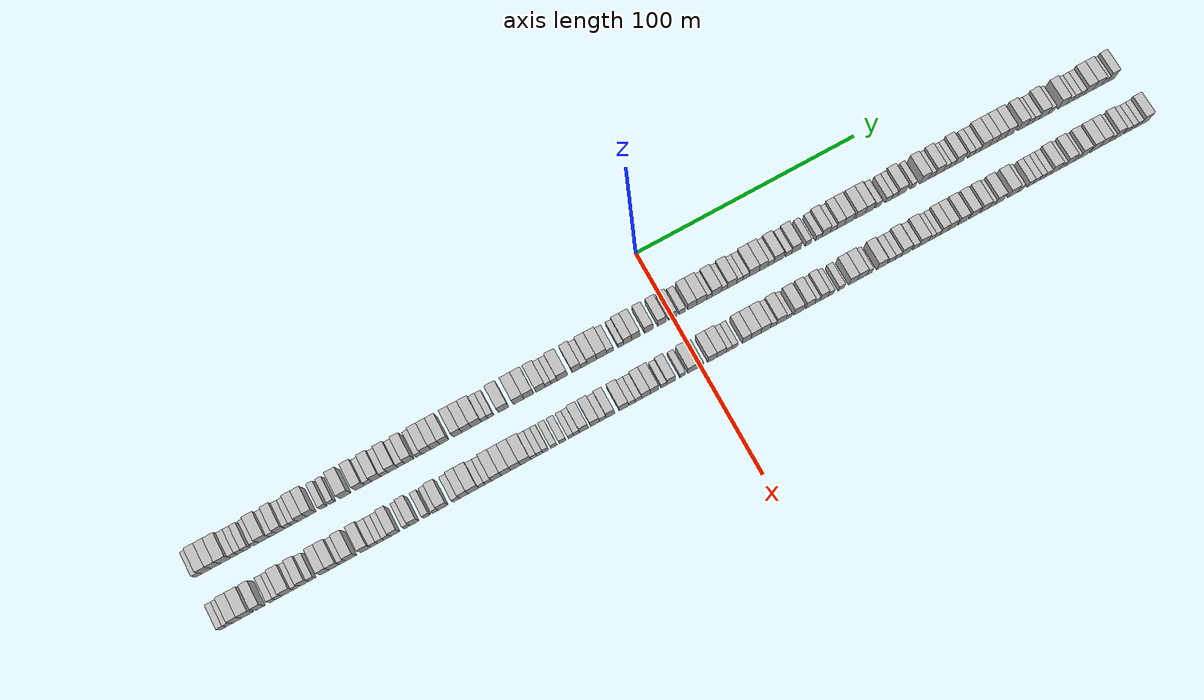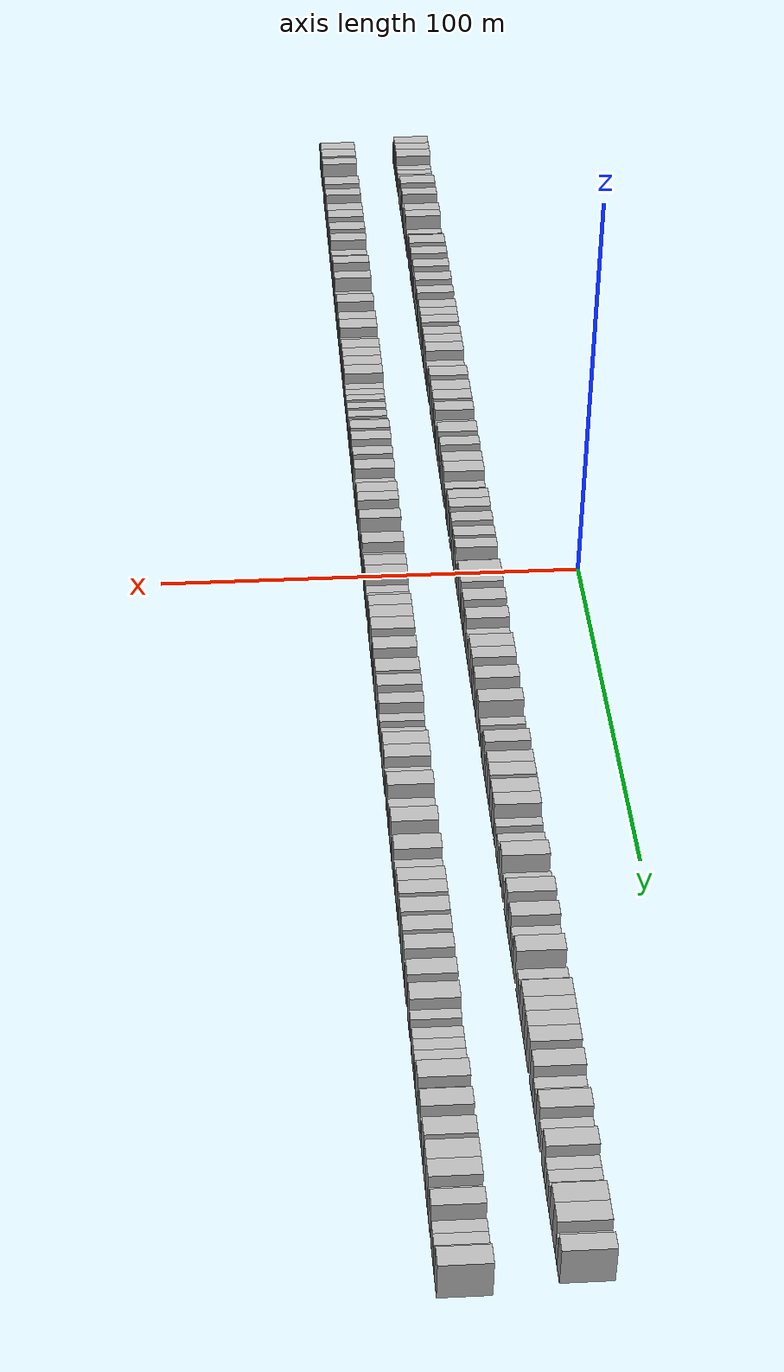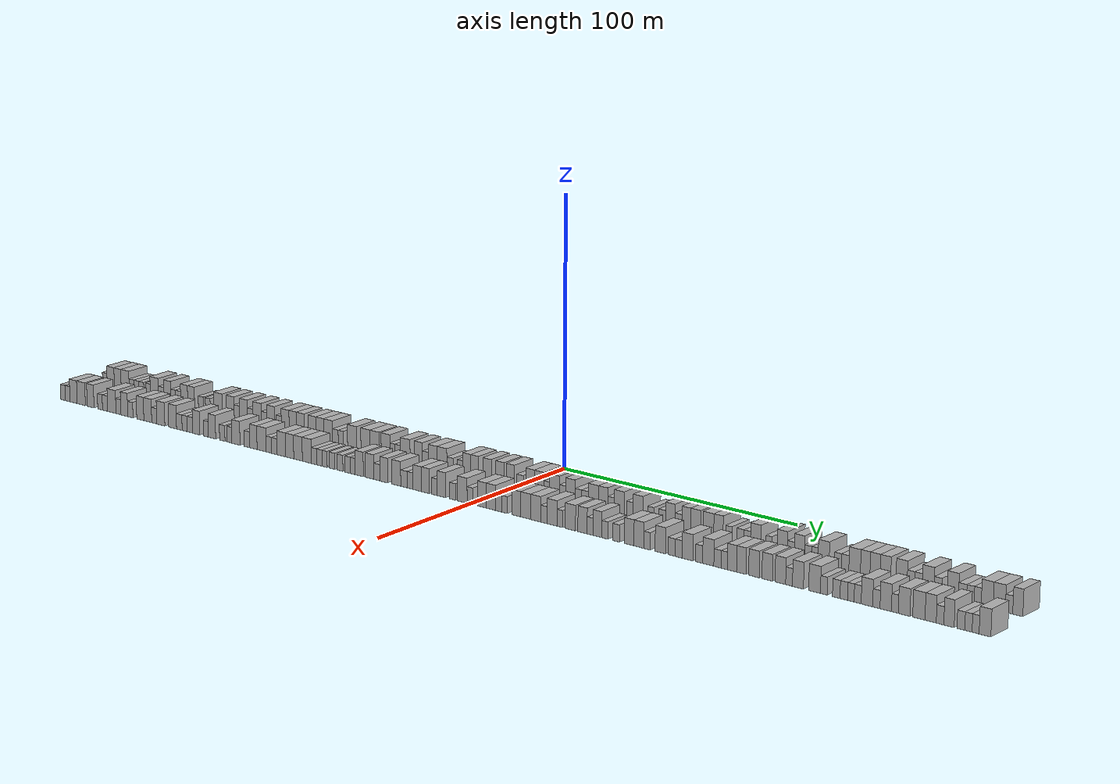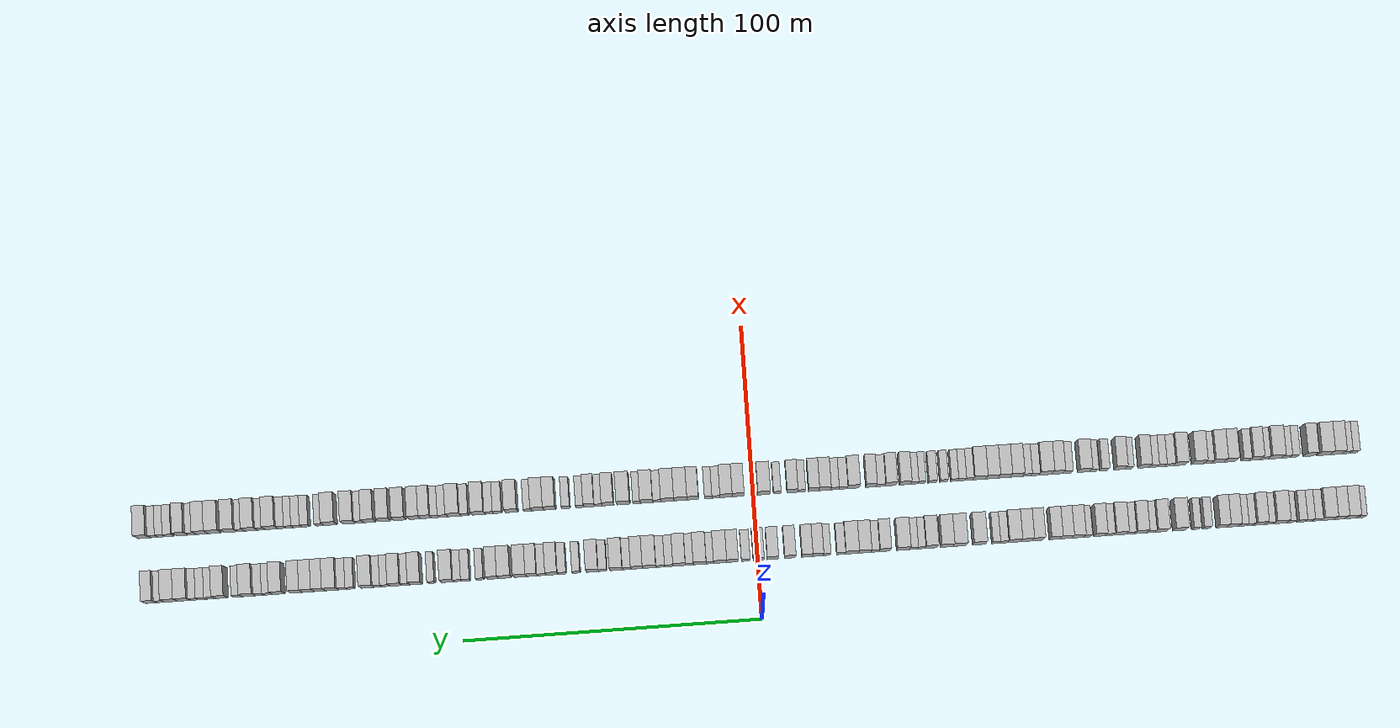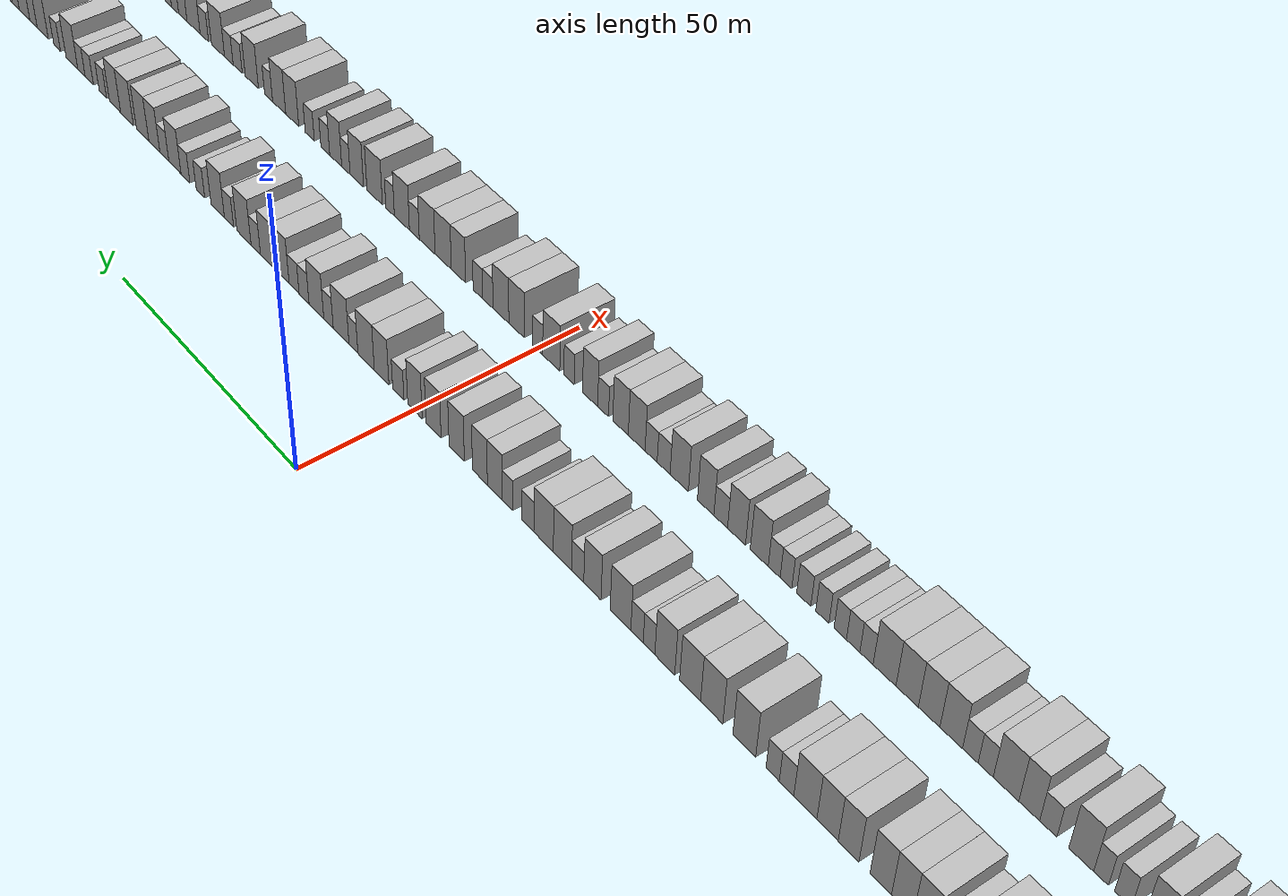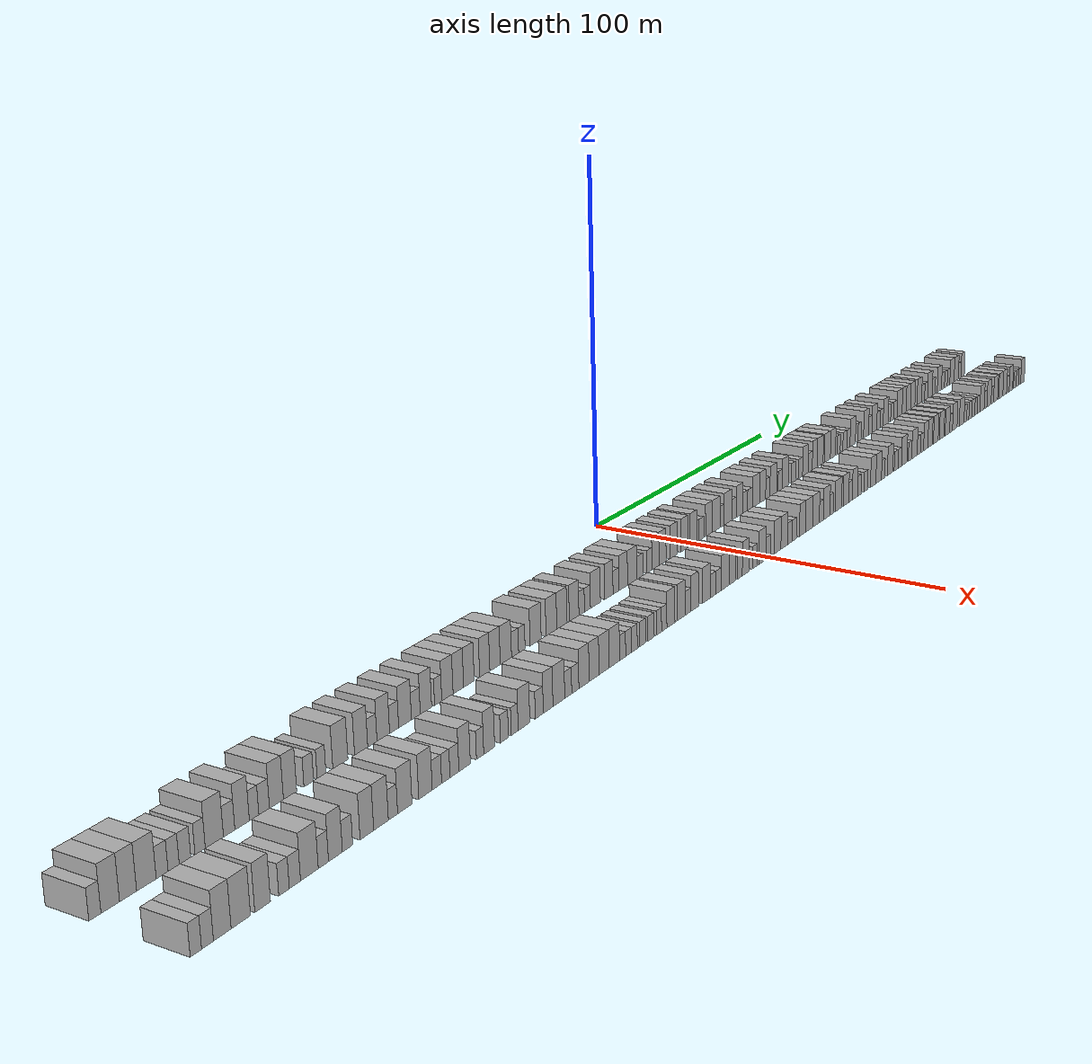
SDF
<sdf version="1.6">
 <world name="default">
  <scene>
   <sky><clouds><speed>12</speed></clouds></sky>
   <ambient>0.4 0.4 0.4 1</ambient>
   <background>0.7 0.7 0.7 1</background>
   <shadows>1</shadows>
  </scene>
  <gravity>0 0 -9.8066</gravity>
  <magnetic_field>6e-06 2.3e-05 -4.2e-05</magnetic_field>
  <physics default="0" name="default_physics" type="ode">
   <ode>
    <solver>
     <type>quick</type>
     <iters>10</iters>
     <sor>1.0</sor>
     <use_dynamic_moi_rescaling>0</use_dynamic_moi_rescaling>
    </solver>
    <constraints>
     <cfm>0</cfm>
     <erp>0.2</erp>
     <contact_max_correcting_vel>100</contact_max_correcting_vel>
     <contact_surface_layer>0.001</contact_surface_layer>
    </constraints>
   </ode>
   <max_step_size>0.004</max_step_size>
   <real_time_factor>1</real_time_factor>
   <real_time_update_rate>250</real_time_update_rate>
  </physics>
  <light name="sun" type="directional">
   <pose>0 0 10 0 0 0</pose>
   <diffuse>0.8 0.8 0.8 1</diffuse>
   <specular>0.2 0.2 0.2 1</specular>
   <attenuation>
    <range>1000</range>
    <constant>0.9</constant>
    <linear>0.01</linear>
    <quadratic>0.001</quadratic>
   </attenuation>
   <direction>-0.5 0.1 -0.9</direction>
  </light>
  <model name="building_1">
   <static>1</static>
   <pose>25.0000 -202.7227 0 0.000000 0.000000 0.000000</pose>
   <link name="link">
    <pose>0 0 3.00 0 0 0</pose>
    <collision name="collision"><geometry><box><size>10.0000 2.5547 6.0000</size></box></geometry></collision>
    <visual name="visual">
     <cast_shadows>0</cast_shadows>
     <geometry><box><size>10.0000 2.5547 6.0000</size></box></geometry>
     <material>
      <script>
       <uri>model://HANNAS_wall/materials/scripts</uri>
       <uri>model://HANNAS_wall/materials/textures</uri>
       <name>vrc/HANNAS_wall</name>
      </script>
     </material>
    </visual>
   </link>
  </model>
  <model name="building_2">
   <static>1</static>
   <pose>25.0000 -199.4642 0 0.000000 0.000000 0.000000</pose>
   <link name="link">
    <pose>0 0 4.50 0 0 0</pose>
    <collision name="collision"><geometry><box><size>10.0000 3.9621 9.0000</size></box></geometry></collision>
    <visual name="visual">
     <cast_shadows>0</cast_shadows>
     <geometry><box><size>10.0000 3.9621 9.0000</size></box></geometry>
     <material>
      <script>
       <uri>model://HANNAS_wall/materials/scripts</uri>
       <uri>model://HANNAS_wall/materials/textures</uri>
       <name>vrc/HANNAS_wall</name>
      </script>
     </material>
    </visual>
   </link>
  </model>
  <model name="building_3">
   <static>1</static>
   <pose>25.0000 -195.6137 0 0.000000 0.000000 0.000000</pose>
   <link name="link">
    <pose>0 0 4.50 0 0 0</pose>
    <collision name="collision"><geometry><box><size>10.0000 3.7389 9.0000</size></box></geometry></collision>
    <visual name="visual">
     <cast_shadows>0</cast_shadows>
     <geometry><box><size>10.0000 3.7389 9.0000</size></box></geometry>
     <material>
      <script>
       <uri>model://HANNAS_wall/materials/scripts</uri>
       <uri>model://HANNAS_wall/materials/textures</uri>
       <name>vrc/HANNAS_wall</name>
      </script>
     </material>
    </visual>
   </link>
  </model>
  <model name="building_4">
   <static>1</static>
   <pose>25.0000 -191.5522 0 0.000000 0.000000 0.000000</pose>
   <link name="link">
    <pose>0 0 4.50 0 0 0</pose>
    <collision name="collision"><geometry><box><size>10.0000 4.3840 9.0000</size></box></geometry></collision>
    <visual name="visual">
     <cast_shadows>0</cast_shadows>
     <geometry><box><size>10.0000 4.3840 9.0000</size></box></geometry>
     <material>
      <script>
       <uri>model://HANNAS_wall/materials/scripts</uri>
       <uri>model://HANNAS_wall/materials/textures</uri>
       <name>vrc/HANNAS_wall</name>
      </script>
     </material>
    </visual>
   </link>
  </model>
  <model name="building_5">
   <static>1</static>
   <pose>25.0000 -188.0011 0 0.000000 0.000000 0.000000</pose>
   <link name="link">
    <pose>0 0 3.00 0 0 0</pose>
    <collision name="collision"><geometry><box><size>10.0000 2.7184 6.0000</size></box></geometry></collision>
    <visual name="visual">
     <cast_shadows>0</cast_shadows>
     <geometry><box><size>10.0000 2.7184 6.0000</size></box></geometry>
     <material>
      <script>
       <uri>model://HANNAS_wall/materials/scripts</uri>
       <uri>model://HANNAS_wall/materials/textures</uri>
       <name>vrc/HANNAS_wall</name>
      </script>
     </material>
    </visual>
   </link>
  </model>
  <model name="building_6">
   <static>1</static>
   <pose>25.0000 -185.3521 0 0.000000 0.000000 0.000000</pose>
   <link name="link">
    <pose>0 0 3.00 0 0 0</pose>
    <collision name="collision"><geometry><box><size>10.0000 2.5795 6.0000</size></box></geometry></collision>
    <visual name="visual">
     <cast_shadows>0</cast_shadows>
     <geometry><box><size>10.0000 2.5795 6.0000</size></box></geometry>
     <material>
      <script>
       <uri>model://HANNAS_wall/materials/scripts</uri>
       <uri>model://HANNAS_wall/materials/textures</uri>
       <name>vrc/HANNAS_wall</name>
      </script>
     </material>
    </visual>
   </link>
  </model>
  <model name="building_7">
   <static>1</static>
   <pose>25.0000 -182.6948 0 0.000000 0.000000 0.000000</pose>
   <link name="link">
    <pose>0 0 3.00 0 0 0</pose>
    <collision name="collision"><geometry><box><size>10.0000 2.7350 6.0000</size></box></geometry></collision>
    <visual name="visual">
     <cast_shadows>0</cast_shadows>
     <geometry><box><size>10.0000 2.7350 6.0000</size></box></geometry>
     <material>
      <script>
       <uri>model://HANNAS_wall/materials/scripts</uri>
       <uri>model://HANNAS_wall/materials/textures</uri>
       <name>vrc/HANNAS_wall</name>
      </script>
     </material>
    </visual>
   </link>
  </model>
  <model name="building_8">
   <static>1</static>
   <pose>25.0000 -179.0899 0 0.000000 0.000000 0.000000</pose>
   <link name="link">
    <pose>0 0 3.00 0 0 0</pose>
    <collision name="collision"><geometry><box><size>10.0000 2.4749 6.0000</size></box></geometry></collision>
    <visual name="visual">
     <cast_shadows>0</cast_shadows>
     <geometry><box><size>10.0000 2.4749 6.0000</size></box></geometry>
     <material>
      <script>
       <uri>model://HANNAS_wall/materials/scripts</uri>
       <uri>model://HANNAS_wall/materials/textures</uri>
       <name>vrc/HANNAS_wall</name>
      </script>
     </material>
    </visual>
   </link>
  </model>
  <model name="building_9">
   <static>1</static>
   <pose>25.0000 -175.6218 0 0.000000 0.000000 0.000000</pose>
   <link name="link">
    <pose>0 0 4.50 0 0 0</pose>
    <collision name="collision"><geometry><box><size>10.0000 4.4612 9.0000</size></box></geometry></collision>
    <visual name="visual">
     <cast_shadows>0</cast_shadows>
     <geometry><box><size>10.0000 4.4612 9.0000</size></box></geometry>
     <material>
      <script>
       <uri>model://HANNAS_wall/materials/scripts</uri>
       <uri>model://HANNAS_wall/materials/textures</uri>
       <name>vrc/HANNAS_wall</name>
      </script>
     </material>
    </visual>
   </link>
  </model>
  <model name="building_10">
   <static>1</static>
   <pose>25.0000 -171.9620 0 0.000000 0.000000 0.000000</pose>
   <link name="link">
    <pose>0 0 3.00 0 0 0</pose>
    <collision name="collision"><geometry><box><size>10.0000 2.8583 6.0000</size></box></geometry></collision>
    <visual name="visual">
     <cast_shadows>0</cast_shadows>
     <geometry><box><size>10.0000 2.8583 6.0000</size></box></geometry>
     <material>
      <script>
       <uri>model://HANNAS_wall/materials/scripts</uri>
       <uri>model://HANNAS_wall/materials/textures</uri>
       <name>vrc/HANNAS_wall</name>
      </script>
     </material>
    </visual>
   </link>
  </model>
  <model name="building_11">
   <static>1</static>
   <pose>25.0000 -168.6852 0 0.000000 0.000000 0.000000</pose>
   <link name="link">
    <pose>0 0 4.50 0 0 0</pose>
    <collision name="collision"><geometry><box><size>10.0000 3.6953 9.0000</size></box></geometry></collision>
    <visual name="visual">
     <cast_shadows>0</cast_shadows>
     <geometry><box><size>10.0000 3.6953 9.0000</size></box></geometry>
     <material>
      <script>
       <uri>model://HANNAS_wall/materials/scripts</uri>
       <uri>model://HANNAS_wall/materials/textures</uri>
       <name>vrc/HANNAS_wall</name>
      </script>
     </material>
    </visual>
   </link>
  </model>
  <model name="building_12">
   <static>1</static>
   <pose>25.0000 -165.6079 0 0.000000 0.000000 0.000000</pose>
   <link name="link">
    <pose>0 0 3.00 0 0 0</pose>
    <collision name="collision"><geometry><box><size>10.0000 2.4591 6.0000</size></box></geometry></collision>
    <visual name="visual">
     <cast_shadows>0</cast_shadows>
     <geometry><box><size>10.0000 2.4591 6.0000</size></box></geometry>
     <material>
      <script>
       <uri>model://HANNAS_wall/materials/scripts</uri>
       <uri>model://HANNAS_wall/materials/textures</uri>
       <name>vrc/HANNAS_wall</name>
      </script>
     </material>
    </visual>
   </link>
  </model>
  <model name="building_13">
   <static>1</static>
   <pose>25.0000 -162.9786 0 0.000000 0.000000 0.000000</pose>
   <link name="link">
    <pose>0 0 3.00 0 0 0</pose>
    <collision name="collision"><geometry><box><size>10.0000 2.7996 6.0000</size></box></geometry></collision>
    <visual name="visual">
     <cast_shadows>0</cast_shadows>
     <geometry><box><size>10.0000 2.7996 6.0000</size></box></geometry>
     <material>
      <script>
       <uri>model://HANNAS_wall/materials/scripts</uri>
       <uri>model://HANNAS_wall/materials/textures</uri>
       <name>vrc/HANNAS_wall</name>
      </script>
     </material>
    </visual>
   </link>
  </model>
  <model name="building_14">
   <static>1</static>
   <pose>25.0000 -159.7097 0 0.000000 0.000000 0.000000</pose>
   <link name="link">
    <pose>0 0 4.50 0 0 0</pose>
    <collision name="collision"><geometry><box><size>10.0000 3.7382 9.0000</size></box></geometry></collision>
    <visual name="visual">
     <cast_shadows>0</cast_shadows>
     <geometry><box><size>10.0000 3.7382 9.0000</size></box></geometry>
     <material>
      <script>
       <uri>model://HANNAS_wall/materials/scripts</uri>
       <uri>model://HANNAS_wall/materials/textures</uri>
       <name>vrc/HANNAS_wall</name>
      </script>
     </material>
    </visual>
   </link>
  </model>
  <model name="building_15">
   <static>1</static>
   <pose>25.0000 -156.0241 0 0.000000 0.000000 0.000000</pose>
   <link name="link">
    <pose>0 0 4.50 0 0 0</pose>
    <collision name="collision"><geometry><box><size>10.0000 3.6329 9.0000</size></box></geometry></collision>
    <visual name="visual">
     <cast_shadows>0</cast_shadows>
     <geometry><box><size>10.0000 3.6329 9.0000</size></box></geometry>
     <material>
      <script>
       <uri>model://HANNAS_wall/materials/scripts</uri>
       <uri>model://HANNAS_wall/materials/textures</uri>
       <name>vrc/HANNAS_wall</name>
      </script>
     </material>
    </visual>
   </link>
  </model>
  <model name="building_16">
   <static>1</static>
   <pose>25.0000 -150.8501 0 0.000000 0.000000 0.000000</pose>
   <link name="link">
    <pose>0 0 3.00 0 0 0</pose>
    <collision name="collision"><geometry><box><size>10.0000 2.7150 6.0000</size></box></geometry></collision>
    <visual name="visual">
     <cast_shadows>0</cast_shadows>
     <geometry><box><size>10.0000 2.7150 6.0000</size></box></geometry>
     <material>
      <script>
       <uri>model://HANNAS_wall/materials/scripts</uri>
       <uri>model://HANNAS_wall/materials/textures</uri>
       <name>vrc/HANNAS_wall</name>
      </script>
     </material>
    </visual>
   </link>
  </model>
  <model name="building_17">
   <static>1</static>
   <pose>25.0000 -147.2384 0 0.000000 0.000000 0.000000</pose>
   <link name="link">
    <pose>0 0 3.00 0 0 0</pose>
    <collision name="collision"><geometry><box><size>10.0000 2.5084 6.0000</size></box></geometry></collision>
    <visual name="visual">
     <cast_shadows>0</cast_shadows>
     <geometry><box><size>10.0000 2.5084 6.0000</size></box></geometry>
     <material>
      <script>
       <uri>model://HANNAS_wall/materials/scripts</uri>
       <uri>model://HANNAS_wall/materials/textures</uri>
       <name>vrc/HANNAS_wall</name>
      </script>
     </material>
    </visual>
   </link>
  </model>
  <model name="building_18">
   <static>1</static>
   <pose>25.0000 -141.7645 0 0.000000 0.000000 0.000000</pose>
   <link name="link">
    <pose>0 0 4.50 0 0 0</pose>
    <collision name="collision"><geometry><box><size>10.0000 4.4394 9.0000</size></box></geometry></collision>
    <visual name="visual">
     <cast_shadows>0</cast_shadows>
     <geometry><box><size>10.0000 4.4394 9.0000</size></box></geometry>
     <material>
      <script>
       <uri>model://HANNAS_wall/materials/scripts</uri>
       <uri>model://HANNAS_wall/materials/textures</uri>
       <name>vrc/HANNAS_wall</name>
      </script>
     </material>
    </visual>
   </link>
  </model>
  <model name="building_19">
   <static>1</static>
   <pose>25.0000 -135.5468 0 0.000000 0.000000 0.000000</pose>
   <link name="link">
    <pose>0 0 4.50 0 0 0</pose>
    <collision name="collision"><geometry><box><size>10.0000 3.9960 9.0000</size></box></geometry></collision>
    <visual name="visual">
     <cast_shadows>0</cast_shadows>
     <geometry><box><size>10.0000 3.9960 9.0000</size></box></geometry>
     <material>
      <script>
       <uri>model://HANNAS_wall/materials/scripts</uri>
       <uri>model://HANNAS_wall/materials/textures</uri>
       <name>vrc/HANNAS_wall</name>
      </script>
     </material>
    </visual>
   </link>
  </model>
  <model name="building_20">
   <static>1</static>
   <pose>25.0000 -132.1186 0 0.000000 0.000000 0.000000</pose>
   <link name="link">
    <pose>0 0 3.00 0 0 0</pose>
    <collision name="collision"><geometry><box><size>10.0000 2.8604 6.0000</size></box></geometry></collision>
    <visual name="visual">
     <cast_shadows>0</cast_shadows>
     <geometry><box><size>10.0000 2.8604 6.0000</size></box></geometry>
     <material>
      <script>
       <uri>model://HANNAS_wall/materials/scripts</uri>
       <uri>model://HANNAS_wall/materials/textures</uri>
       <name>vrc/HANNAS_wall</name>
      </script>
     </material>
    </visual>
   </link>
  </model>
  <model name="building_21">
   <static>1</static>
   <pose>25.0000 -128.6998 0 0.000000 0.000000 0.000000</pose>
   <link name="link">
    <pose>0 0 4.50 0 0 0</pose>
    <collision name="collision"><geometry><box><size>10.0000 3.9771 9.0000</size></box></geometry></collision>
    <visual name="visual">
     <cast_shadows>0</cast_shadows>
     <geometry><box><size>10.0000 3.9771 9.0000</size></box></geometry>
     <material>
      <script>
       <uri>model://HANNAS_wall/materials/scripts</uri>
       <uri>model://HANNAS_wall/materials/textures</uri>
       <name>vrc/HANNAS_wall</name>
      </script>
     </material>
    </visual>
   </link>
  </model>
  <model name="building_22">
   <static>1</static>
   <pose>25.0000 -125.2669 0 0.000000 0.000000 0.000000</pose>
   <link name="link">
    <pose>0 0 3.00 0 0 0</pose>
    <collision name="collision"><geometry><box><size>10.0000 2.8887 6.0000</size></box></geometry></collision>
    <visual name="visual">
     <cast_shadows>0</cast_shadows>
     <geometry><box><size>10.0000 2.8887 6.0000</size></box></geometry>
     <material>
      <script>
       <uri>model://HANNAS_wall/materials/scripts</uri>
       <uri>model://HANNAS_wall/materials/textures</uri>
       <name>vrc/HANNAS_wall</name>
      </script>
     </material>
    </visual>
   </link>
  </model>
  <model name="building_23">
   <static>1</static>
   <pose>25.0000 -121.7365 0 0.000000 0.000000 0.000000</pose>
   <link name="link">
    <pose>0 0 4.50 0 0 0</pose>
    <collision name="collision"><geometry><box><size>10.0000 4.1721 9.0000</size></box></geometry></collision>
    <visual name="visual">
     <cast_shadows>0</cast_shadows>
     <geometry><box><size>10.0000 4.1721 9.0000</size></box></geometry>
     <material>
      <script>
       <uri>model://HANNAS_wall/materials/scripts</uri>
       <uri>model://HANNAS_wall/materials/textures</uri>
       <name>vrc/HANNAS_wall</name>
      </script>
     </material>
    </visual>
   </link>
  </model>
  <model name="building_24">
   <static>1</static>
   <pose>25.0000 -118.1904 0 0.000000 0.000000 0.000000</pose>
   <link name="link">
    <pose>0 0 3.00 0 0 0</pose>
    <collision name="collision"><geometry><box><size>10.0000 2.9200 6.0000</size></box></geometry></collision>
    <visual name="visual">
     <cast_shadows>0</cast_shadows>
     <geometry><box><size>10.0000 2.9200 6.0000</size></box></geometry>
     <material>
      <script>
       <uri>model://HANNAS_wall/materials/scripts</uri>
       <uri>model://HANNAS_wall/materials/textures</uri>
       <name>vrc/HANNAS_wall</name>
      </script>
     </material>
    </visual>
   </link>
  </model>
  <model name="building_25">
   <static>1</static>
   <pose>25.0000 -114.8295 0 0.000000 0.000000 0.000000</pose>
   <link name="link">
    <pose>0 0 4.50 0 0 0</pose>
    <collision name="collision"><geometry><box><size>10.0000 3.8018 9.0000</size></box></geometry></collision>
    <visual name="visual">
     <cast_shadows>0</cast_shadows>
     <geometry><box><size>10.0000 3.8018 9.0000</size></box></geometry>
     <material>
      <script>
       <uri>model://HANNAS_wall/materials/scripts</uri>
       <uri>model://HANNAS_wall/materials/textures</uri>
       <name>vrc/HANNAS_wall</name>
      </script>
     </material>
    </visual>
   </link>
  </model>
  <model name="building_26">
   <static>1</static>
   <pose>25.0000 -110.6860 0 0.000000 0.000000 0.000000</pose>
   <link name="link">
    <pose>0 0 3.00 0 0 0</pose>
    <collision name="collision"><geometry><box><size>10.0000 2.4853 6.0000</size></box></geometry></collision>
    <visual name="visual">
     <cast_shadows>0</cast_shadows>
     <geometry><box><size>10.0000 2.4853 6.0000</size></box></geometry>
     <material>
      <script>
       <uri>model://HANNAS_wall/materials/scripts</uri>
       <uri>model://HANNAS_wall/materials/textures</uri>
       <name>vrc/HANNAS_wall</name>
      </script>
     </material>
    </visual>
   </link>
  </model>
  <model name="building_27">
   <static>1</static>
   <pose>25.0000 -107.4767 0 0.000000 0.000000 0.000000</pose>
   <link name="link">
    <pose>0 0 4.50 0 0 0</pose>
    <collision name="collision"><geometry><box><size>10.0000 3.9333 9.0000</size></box></geometry></collision>
    <visual name="visual">
     <cast_shadows>0</cast_shadows>
     <geometry><box><size>10.0000 3.9333 9.0000</size></box></geometry>
     <material>
      <script>
       <uri>model://HANNAS_wall/materials/scripts</uri>
       <uri>model://HANNAS_wall/materials/textures</uri>
       <name>vrc/HANNAS_wall</name>
      </script>
     </material>
    </visual>
   </link>
  </model>
  <model name="building_28">
   <static>1</static>
   <pose>25.0000 -103.6304 0 0.000000 0.000000 0.000000</pose>
   <link name="link">
    <pose>0 0 4.50 0 0 0</pose>
    <collision name="collision"><geometry><box><size>10.0000 3.7592 9.0000</size></box></geometry></collision>
    <visual name="visual">
     <cast_shadows>0</cast_shadows>
     <geometry><box><size>10.0000 3.7592 9.0000</size></box></geometry>
     <material>
      <script>
       <uri>model://HANNAS_wall/materials/scripts</uri>
       <uri>model://HANNAS_wall/materials/textures</uri>
       <name>vrc/HANNAS_wall</name>
      </script>
     </material>
    </visual>
   </link>
  </model>
  <model name="building_29">
   <static>1</static>
   <pose>25.0000 -99.8501 0 0.000000 0.000000 0.000000</pose>
   <link name="link">
    <pose>0 0 4.50 0 0 0</pose>
    <collision name="collision"><geometry><box><size>10.0000 3.8014 9.0000</size></box></geometry></collision>
    <visual name="visual">
     <cast_shadows>0</cast_shadows>
     <geometry><box><size>10.0000 3.8014 9.0000</size></box></geometry>
     <material>
      <script>
       <uri>model://HANNAS_wall/materials/scripts</uri>
       <uri>model://HANNAS_wall/materials/textures</uri>
       <name>vrc/HANNAS_wall</name>
      </script>
     </material>
    </visual>
   </link>
  </model>
  <model name="building_30">
   <static>1</static>
   <pose>25.0000 -94.0682 0 0.000000 0.000000 0.000000</pose>
   <link name="link">
    <pose>0 0 4.50 0 0 0</pose>
    <collision name="collision"><geometry><box><size>10.0000 3.7626 9.0000</size></box></geometry></collision>
    <visual name="visual">
     <cast_shadows>0</cast_shadows>
     <geometry><box><size>10.0000 3.7626 9.0000</size></box></geometry>
     <material>
      <script>
       <uri>model://HANNAS_wall/materials/scripts</uri>
       <uri>model://HANNAS_wall/materials/textures</uri>
       <name>vrc/HANNAS_wall</name>
      </script>
     </material>
    </visual>
   </link>
  </model>
  <model name="building_31">
   <static>1</static>
   <pose>25.0000 -90.2141 0 0.000000 0.000000 0.000000</pose>
   <link name="link">
    <pose>0 0 4.50 0 0 0</pose>
    <collision name="collision"><geometry><box><size>10.0000 3.9455 9.0000</size></box></geometry></collision>
    <visual name="visual">
     <cast_shadows>0</cast_shadows>
     <geometry><box><size>10.0000 3.9455 9.0000</size></box></geometry>
     <material>
      <script>
       <uri>model://HANNAS_wall/materials/scripts</uri>
       <uri>model://HANNAS_wall/materials/textures</uri>
       <name>vrc/HANNAS_wall</name>
      </script>
     </material>
    </visual>
   </link>
  </model>
  <model name="building_32">
   <static>1</static>
   <pose>25.0000 -86.0812 0 0.000000 0.000000 0.000000</pose>
   <link name="link">
    <pose>0 0 4.50 0 0 0</pose>
    <collision name="collision"><geometry><box><size>10.0000 4.3205 9.0000</size></box></geometry></collision>
    <visual name="visual">
     <cast_shadows>0</cast_shadows>
     <geometry><box><size>10.0000 4.3205 9.0000</size></box></geometry>
     <material>
      <script>
       <uri>model://HANNAS_wall/materials/scripts</uri>
       <uri>model://HANNAS_wall/materials/textures</uri>
       <name>vrc/HANNAS_wall</name>
      </script>
     </material>
    </visual>
   </link>
  </model>
  <model name="building_33">
   <static>1</static>
   <pose>25.0000 -82.5357 0 0.000000 0.000000 0.000000</pose>
   <link name="link">
    <pose>0 0 3.00 0 0 0</pose>
    <collision name="collision"><geometry><box><size>10.0000 2.7704 6.0000</size></box></geometry></collision>
    <visual name="visual">
     <cast_shadows>0</cast_shadows>
     <geometry><box><size>10.0000 2.7704 6.0000</size></box></geometry>
     <material>
      <script>
       <uri>model://HANNAS_wall/materials/scripts</uri>
       <uri>model://HANNAS_wall/materials/textures</uri>
       <name>vrc/HANNAS_wall</name>
      </script>
     </material>
    </visual>
   </link>
  </model>
  <model name="building_34">
   <static>1</static>
   <pose>25.0000 -79.8759 0 0.000000 0.000000 0.000000</pose>
   <link name="link">
    <pose>0 0 3.00 0 0 0</pose>
    <collision name="collision"><geometry><box><size>10.0000 2.5492 6.0000</size></box></geometry></collision>
    <visual name="visual">
     <cast_shadows>0</cast_shadows>
     <geometry><box><size>10.0000 2.5492 6.0000</size></box></geometry>
     <material>
      <script>
       <uri>model://HANNAS_wall/materials/scripts</uri>
       <uri>model://HANNAS_wall/materials/textures</uri>
       <name>vrc/HANNAS_wall</name>
      </script>
     </material>
    </visual>
   </link>
  </model>
  <model name="building_35">
   <static>1</static>
   <pose>25.0000 -74.3576 0 0.000000 0.000000 0.000000</pose>
   <link name="link">
    <pose>0 0 4.50 0 0 0</pose>
    <collision name="collision"><geometry><box><size>10.0000 4.4875 9.0000</size></box></geometry></collision>
    <visual name="visual">
     <cast_shadows>0</cast_shadows>
     <geometry><box><size>10.0000 4.4875 9.0000</size></box></geometry>
     <material>
      <script>
       <uri>model://HANNAS_wall/materials/scripts</uri>
       <uri>model://HANNAS_wall/materials/textures</uri>
       <name>vrc/HANNAS_wall</name>
      </script>
     </material>
    </visual>
   </link>
  </model>
  <model name="building_36">
   <static>1</static>
   <pose>25.0000 -67.8687 0 0.000000 0.000000 0.000000</pose>
   <link name="link">
    <pose>0 0 4.50 0 0 0</pose>
    <collision name="collision"><geometry><box><size>10.0000 4.4902 9.0000</size></box></geometry></collision>
    <visual name="visual">
     <cast_shadows>0</cast_shadows>
     <geometry><box><size>10.0000 4.4902 9.0000</size></box></geometry>
     <material>
      <script>
       <uri>model://HANNAS_wall/materials/scripts</uri>
       <uri>model://HANNAS_wall/materials/textures</uri>
       <name>vrc/HANNAS_wall</name>
      </script>
     </material>
    </visual>
   </link>
  </model>
  <model name="building_37">
   <static>1</static>
   <pose>25.0000 -63.4710 0 0.000000 0.000000 0.000000</pose>
   <link name="link">
    <pose>0 0 4.50 0 0 0</pose>
    <collision name="collision"><geometry><box><size>10.0000 4.3054 9.0000</size></box></geometry></collision>
    <visual name="visual">
     <cast_shadows>0</cast_shadows>
     <geometry><box><size>10.0000 4.3054 9.0000</size></box></geometry>
     <material>
      <script>
       <uri>model://HANNAS_wall/materials/scripts</uri>
       <uri>model://HANNAS_wall/materials/textures</uri>
       <name>vrc/HANNAS_wall</name>
      </script>
     </material>
    </visual>
   </link>
  </model>
  <model name="building_38">
   <static>1</static>
   <pose>25.0000 -58.2366 0 0.000000 0.000000 0.000000</pose>
   <link name="link">
    <pose>0 0 4.50 0 0 0</pose>
    <collision name="collision"><geometry><box><size>10.0000 4.1633 9.0000</size></box></geometry></collision>
    <visual name="visual">
     <cast_shadows>0</cast_shadows>
     <geometry><box><size>10.0000 4.1633 9.0000</size></box></geometry>
     <material>
      <script>
       <uri>model://HANNAS_wall/materials/scripts</uri>
       <uri>model://HANNAS_wall/materials/textures</uri>
       <name>vrc/HANNAS_wall</name>
      </script>
     </material>
    </visual>
   </link>
  </model>
  <model name="building_39">
   <static>1</static>
   <pose>25.0000 -54.9228 0 0.000000 0.000000 0.000000</pose>
   <link name="link">
    <pose>0 0 3.00 0 0 0</pose>
    <collision name="collision"><geometry><box><size>10.0000 2.4642 6.0000</size></box></geometry></collision>
    <visual name="visual">
     <cast_shadows>0</cast_shadows>
     <geometry><box><size>10.0000 2.4642 6.0000</size></box></geometry>
     <material>
      <script>
       <uri>model://HANNAS_wall/materials/scripts</uri>
       <uri>model://HANNAS_wall/materials/textures</uri>
       <name>vrc/HANNAS_wall</name>
      </script>
     </material>
    </visual>
   </link>
  </model>
  <model name="building_40">
   <static>1</static>
   <pose>25.0000 -52.3676 0 0.000000 0.000000 0.000000</pose>
   <link name="link">
    <pose>0 0 3.00 0 0 0</pose>
    <collision name="collision"><geometry><box><size>10.0000 2.6464 6.0000</size></box></geometry></collision>
    <visual name="visual">
     <cast_shadows>0</cast_shadows>
     <geometry><box><size>10.0000 2.6464 6.0000</size></box></geometry>
     <material>
      <script>
       <uri>model://HANNAS_wall/materials/scripts</uri>
       <uri>model://HANNAS_wall/materials/textures</uri>
       <name>vrc/HANNAS_wall</name>
      </script>
     </material>
    </visual>
   </link>
  </model>
  <model name="building_41">
   <static>1</static>
   <pose>25.0000 -48.7996 0 0.000000 0.000000 0.000000</pose>
   <link name="link">
    <pose>0 0 4.50 0 0 0</pose>
    <collision name="collision"><geometry><box><size>10.0000 4.4895 9.0000</size></box></geometry></collision>
    <visual name="visual">
     <cast_shadows>0</cast_shadows>
     <geometry><box><size>10.0000 4.4895 9.0000</size></box></geometry>
     <material>
      <script>
       <uri>model://HANNAS_wall/materials/scripts</uri>
       <uri>model://HANNAS_wall/materials/textures</uri>
       <name>vrc/HANNAS_wall</name>
      </script>
     </material>
    </visual>
   </link>
  </model>
  <model name="building_42">
   <static>1</static>
   <pose>25.0000 -42.6450 0 0.000000 0.000000 0.000000</pose>
   <link name="link">
    <pose>0 0 4.50 0 0 0</pose>
    <collision name="collision"><geometry><box><size>10.0000 3.8197 9.0000</size></box></geometry></collision>
    <visual name="visual">
     <cast_shadows>0</cast_shadows>
     <geometry><box><size>10.0000 3.8197 9.0000</size></box></geometry>
     <material>
      <script>
       <uri>model://HANNAS_wall/materials/scripts</uri>
       <uri>model://HANNAS_wall/materials/textures</uri>
       <name>vrc/HANNAS_wall</name>
      </script>
     </material>
    </visual>
   </link>
  </model>
  <model name="building_43">
   <static>1</static>
   <pose>25.0000 -39.3544 0 0.000000 0.000000 0.000000</pose>
   <link name="link">
    <pose>0 0 3.00 0 0 0</pose>
    <collision name="collision"><geometry><box><size>10.0000 2.7616 6.0000</size></box></geometry></collision>
    <visual name="visual">
     <cast_shadows>0</cast_shadows>
     <geometry><box><size>10.0000 2.7616 6.0000</size></box></geometry>
     <material>
      <script>
       <uri>model://HANNAS_wall/materials/scripts</uri>
       <uri>model://HANNAS_wall/materials/textures</uri>
       <name>vrc/HANNAS_wall</name>
      </script>
     </material>
    </visual>
   </link>
  </model>
  <model name="building_44">
   <static>1</static>
   <pose>25.0000 -35.9110 0 0.000000 0.000000 0.000000</pose>
   <link name="link">
    <pose>0 0 4.50 0 0 0</pose>
    <collision name="collision"><geometry><box><size>10.0000 4.1252 9.0000</size></box></geometry></collision>
    <visual name="visual">
     <cast_shadows>0</cast_shadows>
     <geometry><box><size>10.0000 4.1252 9.0000</size></box></geometry>
     <material>
      <script>
       <uri>model://HANNAS_wall/materials/scripts</uri>
       <uri>model://HANNAS_wall/materials/textures</uri>
       <name>vrc/HANNAS_wall</name>
      </script>
     </material>
    </visual>
   </link>
  </model>
  <model name="building_45">
   <static>1</static>
   <pose>25.0000 -31.6001 0 0.000000 0.000000 0.000000</pose>
   <link name="link">
    <pose>0 0 4.50 0 0 0</pose>
    <collision name="collision"><geometry><box><size>10.0000 4.4965 9.0000</size></box></geometry></collision>
    <visual name="visual">
     <cast_shadows>0</cast_shadows>
     <geometry><box><size>10.0000 4.4965 9.0000</size></box></geometry>
     <material>
      <script>
       <uri>model://HANNAS_wall/materials/scripts</uri>
       <uri>model://HANNAS_wall/materials/textures</uri>
       <name>vrc/HANNAS_wall</name>
      </script>
     </material>
    </visual>
   </link>
  </model>
  <model name="building_46">
   <static>1</static>
   <pose>25.0000 -27.8859 0 0.000000 0.000000 0.000000</pose>
   <link name="link">
    <pose>0 0 3.00 0 0 0</pose>
    <collision name="collision"><geometry><box><size>10.0000 2.9319 6.0000</size></box></geometry></collision>
    <visual name="visual">
     <cast_shadows>0</cast_shadows>
     <geometry><box><size>10.0000 2.9319 6.0000</size></box></geometry>
     <material>
      <script>
       <uri>model://HANNAS_wall/materials/scripts</uri>
       <uri>model://HANNAS_wall/materials/textures</uri>
       <name>vrc/HANNAS_wall</name>
      </script>
     </material>
    </visual>
   </link>
  </model>
  <model name="building_47">
   <static>1</static>
   <pose>25.0000 -23.1822 0 0.000000 0.000000 0.000000</pose>
   <link name="link">
    <pose>0 0 3.00 0 0 0</pose>
    <collision name="collision"><geometry><box><size>10.0000 2.4754 6.0000</size></box></geometry></collision>
    <visual name="visual">
     <cast_shadows>0</cast_shadows>
     <geometry><box><size>10.0000 2.4754 6.0000</size></box></geometry>
     <material>
      <script>
       <uri>model://HANNAS_wall/materials/scripts</uri>
       <uri>model://HANNAS_wall/materials/textures</uri>
       <name>vrc/HANNAS_wall</name>
      </script>
     </material>
    </visual>
   </link>
  </model>
  <model name="building_48">
   <static>1</static>
   <pose>25.0000 -20.1401 0 0.000000 0.000000 0.000000</pose>
   <link name="link">
    <pose>0 0 4.50 0 0 0</pose>
    <collision name="collision"><geometry><box><size>10.0000 3.6088 9.0000</size></box></geometry></collision>
    <visual name="visual">
     <cast_shadows>0</cast_shadows>
     <geometry><box><size>10.0000 3.6088 9.0000</size></box></geometry>
     <material>
      <script>
       <uri>model://HANNAS_wall/materials/scripts</uri>
       <uri>model://HANNAS_wall/materials/textures</uri>
       <name>vrc/HANNAS_wall</name>
      </script>
     </material>
    </visual>
   </link>
  </model>
  <model name="building_49">
   <static>1</static>
   <pose>25.0000 -16.5165 0 0.000000 0.000000 0.000000</pose>
   <link name="link">
    <pose>0 0 4.50 0 0 0</pose>
    <collision name="collision"><geometry><box><size>10.0000 3.6384 9.0000</size></box></geometry></collision>
    <visual name="visual">
     <cast_shadows>0</cast_shadows>
     <geometry><box><size>10.0000 3.6384 9.0000</size></box></geometry>
     <material>
      <script>
       <uri>model://HANNAS_wall/materials/scripts</uri>
       <uri>model://HANNAS_wall/materials/textures</uri>
       <name>vrc/HANNAS_wall</name>
      </script>
     </material>
    </visual>
   </link>
  </model>
  <model name="building_50">
   <static>1</static>
   <pose>25.0000 -10.7964 0 0.000000 0.000000 0.000000</pose>
   <link name="link">
    <pose>0 0 4.50 0 0 0</pose>
    <collision name="collision"><geometry><box><size>10.0000 3.8018 9.0000</size></box></geometry></collision>
    <visual name="visual">
     <cast_shadows>0</cast_shadows>
     <geometry><box><size>10.0000 3.8018 9.0000</size></box></geometry>
     <material>
      <script>
       <uri>model://HANNAS_wall/materials/scripts</uri>
       <uri>model://HANNAS_wall/materials/textures</uri>
       <name>vrc/HANNAS_wall</name>
      </script>
     </material>
    </visual>
   </link>
  </model>
  <model name="building_51">
   <static>1</static>
   <pose>25.0000 -4.9890 0 0.000000 0.000000 0.000000</pose>
   <link name="link">
    <pose>0 0 4.50 0 0 0</pose>
    <collision name="collision"><geometry><box><size>10.0000 3.8128 9.0000</size></box></geometry></collision>
    <visual name="visual">
     <cast_shadows>0</cast_shadows>
     <geometry><box><size>10.0000 3.8128 9.0000</size></box></geometry>
     <material>
      <script>
       <uri>model://HANNAS_wall/materials/scripts</uri>
       <uri>model://HANNAS_wall/materials/textures</uri>
       <name>vrc/HANNAS_wall</name>
      </script>
     </material>
    </visual>
   </link>
  </model>
  <model name="building_52">
   <static>1</static>
   <pose>25.0000 -0.2341 0 0.000000 0.000000 0.000000</pose>
   <link name="link">
    <pose>0 0 4.50 0 0 0</pose>
    <collision name="collision"><geometry><box><size>10.0000 3.6971 9.0000</size></box></geometry></collision>
    <visual name="visual">
     <cast_shadows>0</cast_shadows>
     <geometry><box><size>10.0000 3.6971 9.0000</size></box></geometry>
     <material>
      <script>
       <uri>model://HANNAS_wall/materials/scripts</uri>
       <uri>model://HANNAS_wall/materials/textures</uri>
       <name>vrc/HANNAS_wall</name>
      </script>
     </material>
    </visual>
   </link>
  </model>
  <model name="building_53">
   <static>1</static>
   <pose>25.0000 4.0832 0 0.000000 0.000000 0.000000</pose>
   <link name="link">
    <pose>0 0 3.00 0 0 0</pose>
    <collision name="collision"><geometry><box><size>10.0000 2.9375 6.0000</size></box></geometry></collision>
    <visual name="visual">
     <cast_shadows>0</cast_shadows>
     <geometry><box><size>10.0000 2.9375 6.0000</size></box></geometry>
     <material>
      <script>
       <uri>model://HANNAS_wall/materials/scripts</uri>
       <uri>model://HANNAS_wall/materials/textures</uri>
       <name>vrc/HANNAS_wall</name>
      </script>
     </material>
    </visual>
   </link>
  </model>
  <model name="building_54">
   <static>1</static>
   <pose>25.0000 8.4924 0 0.000000 0.000000 0.000000</pose>
   <link name="link">
    <pose>0 0 4.50 0 0 0</pose>
    <collision name="collision"><geometry><box><size>10.0000 3.8807 9.0000</size></box></geometry></collision>
    <visual name="visual">
     <cast_shadows>0</cast_shadows>
     <geometry><box><size>10.0000 3.8807 9.0000</size></box></geometry>
     <material>
      <script>
       <uri>model://HANNAS_wall/materials/scripts</uri>
       <uri>model://HANNAS_wall/materials/textures</uri>
       <name>vrc/HANNAS_wall</name>
      </script>
     </material>
    </visual>
   </link>
  </model>
  <model name="building_55">
   <static>1</static>
   <pose>25.0000 12.6406 0 0.000000 0.000000 0.000000</pose>
   <link name="link">
    <pose>0 0 4.50 0 0 0</pose>
    <collision name="collision"><geometry><box><size>10.0000 4.4157 9.0000</size></box></geometry></collision>
    <visual name="visual">
     <cast_shadows>0</cast_shadows>
     <geometry><box><size>10.0000 4.4157 9.0000</size></box></geometry>
     <material>
      <script>
       <uri>model://HANNAS_wall/materials/scripts</uri>
       <uri>model://HANNAS_wall/materials/textures</uri>
       <name>vrc/HANNAS_wall</name>
      </script>
     </material>
    </visual>
   </link>
  </model>
  <model name="building_56">
   <static>1</static>
   <pose>25.0000 16.0649 0 0.000000 0.000000 0.000000</pose>
   <link name="link">
    <pose>0 0 3.00 0 0 0</pose>
    <collision name="collision"><geometry><box><size>10.0000 2.4328 6.0000</size></box></geometry></collision>
    <visual name="visual">
     <cast_shadows>0</cast_shadows>
     <geometry><box><size>10.0000 2.4328 6.0000</size></box></geometry>
     <material>
      <script>
       <uri>model://HANNAS_wall/materials/scripts</uri>
       <uri>model://HANNAS_wall/materials/textures</uri>
       <name>vrc/HANNAS_wall</name>
      </script>
     </material>
    </visual>
   </link>
  </model>
  <model name="building_57">
   <static>1</static>
   <pose>25.0000 19.4465 0 0.000000 0.000000 0.000000</pose>
   <link name="link">
    <pose>0 0 4.50 0 0 0</pose>
    <collision name="collision"><geometry><box><size>10.0000 4.3304 9.0000</size></box></geometry></collision>
    <visual name="visual">
     <cast_shadows>0</cast_shadows>
     <geometry><box><size>10.0000 4.3304 9.0000</size></box></geometry>
     <material>
      <script>
       <uri>model://HANNAS_wall/materials/scripts</uri>
       <uri>model://HANNAS_wall/materials/textures</uri>
       <name>vrc/HANNAS_wall</name>
      </script>
     </material>
    </visual>
   </link>
  </model>
  <model name="building_58">
   <static>1</static>
   <pose>25.0000 22.9287 0 0.000000 0.000000 0.000000</pose>
   <link name="link">
    <pose>0 0 3.00 0 0 0</pose>
    <collision name="collision"><geometry><box><size>10.0000 2.6340 6.0000</size></box></geometry></collision>
    <visual name="visual">
     <cast_shadows>0</cast_shadows>
     <geometry><box><size>10.0000 2.6340 6.0000</size></box></geometry>
     <material>
      <script>
       <uri>model://HANNAS_wall/materials/scripts</uri>
       <uri>model://HANNAS_wall/materials/textures</uri>
       <name>vrc/HANNAS_wall</name>
      </script>
     </material>
    </visual>
   </link>
  </model>
  <model name="building_59">
   <static>1</static>
   <pose>25.0000 26.3239 0 0.000000 0.000000 0.000000</pose>
   <link name="link">
    <pose>0 0 4.50 0 0 0</pose>
    <collision name="collision"><geometry><box><size>10.0000 4.1565 9.0000</size></box></geometry></collision>
    <visual name="visual">
     <cast_shadows>0</cast_shadows>
     <geometry><box><size>10.0000 4.1565 9.0000</size></box></geometry>
     <material>
      <script>
       <uri>model://HANNAS_wall/materials/scripts</uri>
       <uri>model://HANNAS_wall/materials/textures</uri>
       <name>vrc/HANNAS_wall</name>
      </script>
     </material>
    </visual>
   </link>
  </model>
  <model name="building_60">
   <static>1</static>
   <pose>25.0000 29.8214 0 0.000000 0.000000 0.000000</pose>
   <link name="link">
    <pose>0 0 3.00 0 0 0</pose>
    <collision name="collision"><geometry><box><size>10.0000 2.8384 6.0000</size></box></geometry></collision>
    <visual name="visual">
     <cast_shadows>0</cast_shadows>
     <geometry><box><size>10.0000 2.8384 6.0000</size></box></geometry>
     <material>
      <script>
       <uri>model://HANNAS_wall/materials/scripts</uri>
       <uri>model://HANNAS_wall/materials/textures</uri>
       <name>vrc/HANNAS_wall</name>
      </script>
     </material>
    </visual>
   </link>
  </model>
  <model name="building_61">
   <static>1</static>
   <pose>25.0000 32.6655 0 0.000000 0.000000 0.000000</pose>
   <link name="link">
    <pose>0 0 3.00 0 0 0</pose>
    <collision name="collision"><geometry><box><size>10.0000 2.8499 6.0000</size></box></geometry></collision>
    <visual name="visual">
     <cast_shadows>0</cast_shadows>
     <geometry><box><size>10.0000 2.8499 6.0000</size></box></geometry>
     <material>
      <script>
       <uri>model://HANNAS_wall/materials/scripts</uri>
       <uri>model://HANNAS_wall/materials/textures</uri>
       <name>vrc/HANNAS_wall</name>
      </script>
     </material>
    </visual>
   </link>
  </model>
  <model name="building_62">
   <static>1</static>
   <pose>25.0000 36.3310 0 0.000000 0.000000 0.000000</pose>
   <link name="link">
    <pose>0 0 4.50 0 0 0</pose>
    <collision name="collision"><geometry><box><size>10.0000 4.4812 9.0000</size></box></geometry></collision>
    <visual name="visual">
     <cast_shadows>0</cast_shadows>
     <geometry><box><size>10.0000 4.4812 9.0000</size></box></geometry>
     <material>
      <script>
       <uri>model://HANNAS_wall/materials/scripts</uri>
       <uri>model://HANNAS_wall/materials/textures</uri>
       <name>vrc/HANNAS_wall</name>
      </script>
     </material>
    </visual>
   </link>
  </model>
  <model name="building_63">
   <static>1</static>
   <pose>25.0000 40.5339 0 0.000000 0.000000 0.000000</pose>
   <link name="link">
    <pose>0 0 4.50 0 0 0</pose>
    <collision name="collision"><geometry><box><size>10.0000 3.9246 9.0000</size></box></geometry></collision>
    <visual name="visual">
     <cast_shadows>0</cast_shadows>
     <geometry><box><size>10.0000 3.9246 9.0000</size></box></geometry>
     <material>
      <script>
       <uri>model://HANNAS_wall/materials/scripts</uri>
       <uri>model://HANNAS_wall/materials/textures</uri>
       <name>vrc/HANNAS_wall</name>
      </script>
     </material>
    </visual>
   </link>
  </model>
  <model name="building_64">
   <static>1</static>
   <pose>25.0000 43.9046 0 0.000000 0.000000 0.000000</pose>
   <link name="link">
    <pose>0 0 3.00 0 0 0</pose>
    <collision name="collision"><geometry><box><size>10.0000 2.8168 6.0000</size></box></geometry></collision>
    <visual name="visual">
     <cast_shadows>0</cast_shadows>
     <geometry><box><size>10.0000 2.8168 6.0000</size></box></geometry>
     <material>
      <script>
       <uri>model://HANNAS_wall/materials/scripts</uri>
       <uri>model://HANNAS_wall/materials/textures</uri>
       <name>vrc/HANNAS_wall</name>
      </script>
     </material>
    </visual>
   </link>
  </model>
  <model name="building_65">
   <static>1</static>
   <pose>25.0000 47.4456 0 0.000000 0.000000 0.000000</pose>
   <link name="link">
    <pose>0 0 4.50 0 0 0</pose>
    <collision name="collision"><geometry><box><size>10.0000 4.2652 9.0000</size></box></geometry></collision>
    <visual name="visual">
     <cast_shadows>0</cast_shadows>
     <geometry><box><size>10.0000 4.2652 9.0000</size></box></geometry>
     <material>
      <script>
       <uri>model://HANNAS_wall/materials/scripts</uri>
       <uri>model://HANNAS_wall/materials/textures</uri>
       <name>vrc/HANNAS_wall</name>
      </script>
     </material>
    </visual>
   </link>
  </model>
  <model name="building_66">
   <static>1</static>
   <pose>25.0000 51.9770 0 0.000000 0.000000 0.000000</pose>
   <link name="link">
    <pose>0 0 3.00 0 0 0</pose>
    <collision name="collision"><geometry><box><size>10.0000 2.7976 6.0000</size></box></geometry></collision>
    <visual name="visual">
     <cast_shadows>0</cast_shadows>
     <geometry><box><size>10.0000 2.7976 6.0000</size></box></geometry>
     <material>
      <script>
       <uri>model://HANNAS_wall/materials/scripts</uri>
       <uri>model://HANNAS_wall/materials/textures</uri>
       <name>vrc/HANNAS_wall</name>
      </script>
     </material>
    </visual>
   </link>
  </model>
  <model name="building_67">
   <static>1</static>
   <pose>25.0000 55.4416 0 0.000000 0.000000 0.000000</pose>
   <link name="link">
    <pose>0 0 4.50 0 0 0</pose>
    <collision name="collision"><geometry><box><size>10.0000 4.1315 9.0000</size></box></geometry></collision>
    <visual name="visual">
     <cast_shadows>0</cast_shadows>
     <geometry><box><size>10.0000 4.1315 9.0000</size></box></geometry>
     <material>
      <script>
       <uri>model://HANNAS_wall/materials/scripts</uri>
       <uri>model://HANNAS_wall/materials/textures</uri>
       <name>vrc/HANNAS_wall</name>
      </script>
     </material>
    </visual>
   </link>
  </model>
  <model name="building_68">
   <static>1</static>
   <pose>25.0000 60.8428 0 0.000000 0.000000 0.000000</pose>
   <link name="link">
    <pose>0 0 3.00 0 0 0</pose>
    <collision name="collision"><geometry><box><size>10.0000 2.6708 6.0000</size></box></geometry></collision>
    <visual name="visual">
     <cast_shadows>0</cast_shadows>
     <geometry><box><size>10.0000 2.6708 6.0000</size></box></geometry>
     <material>
      <script>
       <uri>model://HANNAS_wall/materials/scripts</uri>
       <uri>model://HANNAS_wall/materials/textures</uri>
       <name>vrc/HANNAS_wall</name>
      </script>
     </material>
    </visual>
   </link>
  </model>
  <model name="building_69">
   <static>1</static>
   <pose>25.0000 65.5975 0 0.000000 0.000000 0.000000</pose>
   <link name="link">
    <pose>0 0 3.00 0 0 0</pose>
    <collision name="collision"><geometry><box><size>10.0000 2.8386 6.0000</size></box></geometry></collision>
    <visual name="visual">
     <cast_shadows>0</cast_shadows>
     <geometry><box><size>10.0000 2.8386 6.0000</size></box></geometry>
     <material>
      <script>
       <uri>model://HANNAS_wall/materials/scripts</uri>
       <uri>model://HANNAS_wall/materials/textures</uri>
       <name>vrc/HANNAS_wall</name>
      </script>
     </material>
    </visual>
   </link>
  </model>
  <model name="building_70">
   <static>1</static>
   <pose>25.0000 68.9816 0 0.000000 0.000000 0.000000</pose>
   <link name="link">
    <pose>0 0 4.50 0 0 0</pose>
    <collision name="collision"><geometry><box><size>10.0000 3.9295 9.0000</size></box></geometry></collision>
    <visual name="visual">
     <cast_shadows>0</cast_shadows>
     <geometry><box><size>10.0000 3.9295 9.0000</size></box></geometry>
     <material>
      <script>
       <uri>model://HANNAS_wall/materials/scripts</uri>
       <uri>model://HANNAS_wall/materials/textures</uri>
       <name>vrc/HANNAS_wall</name>
      </script>
     </material>
    </visual>
   </link>
  </model>
  <model name="building_71">
   <static>1</static>
   <pose>25.0000 72.4095 0 0.000000 0.000000 0.000000</pose>
   <link name="link">
    <pose>0 0 3.00 0 0 0</pose>
    <collision name="collision"><geometry><box><size>10.0000 2.9262 6.0000</size></box></geometry></collision>
    <visual name="visual">
     <cast_shadows>0</cast_shadows>
     <geometry><box><size>10.0000 2.9262 6.0000</size></box></geometry>
     <material>
      <script>
       <uri>model://HANNAS_wall/materials/scripts</uri>
       <uri>model://HANNAS_wall/materials/textures</uri>
       <name>vrc/HANNAS_wall</name>
      </script>
     </material>
    </visual>
   </link>
  </model>
  <model name="building_72">
   <static>1</static>
   <pose>25.0000 75.6916 0 0.000000 0.000000 0.000000</pose>
   <link name="link">
    <pose>0 0 4.50 0 0 0</pose>
    <collision name="collision"><geometry><box><size>10.0000 3.6381 9.0000</size></box></geometry></collision>
    <visual name="visual">
     <cast_shadows>0</cast_shadows>
     <geometry><box><size>10.0000 3.6381 9.0000</size></box></geometry>
     <material>
      <script>
       <uri>model://HANNAS_wall/materials/scripts</uri>
       <uri>model://HANNAS_wall/materials/textures</uri>
       <name>vrc/HANNAS_wall</name>
      </script>
     </material>
    </visual>
   </link>
  </model>
  <model name="building_73">
   <static>1</static>
   <pose>25.0000 79.5745 0 0.000000 0.000000 0.000000</pose>
   <link name="link">
    <pose>0 0 4.50 0 0 0</pose>
    <collision name="collision"><geometry><box><size>10.0000 4.1278 9.0000</size></box></geometry></collision>
    <visual name="visual">
     <cast_shadows>0</cast_shadows>
     <geometry><box><size>10.0000 4.1278 9.0000</size></box></geometry>
     <material>
      <script>
       <uri>model://HANNAS_wall/materials/scripts</uri>
       <uri>model://HANNAS_wall/materials/textures</uri>
       <name>vrc/HANNAS_wall</name>
      </script>
     </material>
    </visual>
   </link>
  </model>
  <model name="building_74">
   <static>1</static>
   <pose>25.0000 84.8035 0 0.000000 0.000000 0.000000</pose>
   <link name="link">
    <pose>0 0 4.50 0 0 0</pose>
    <collision name="collision"><geometry><box><size>10.0000 4.3300 9.0000</size></box></geometry></collision>
    <visual name="visual">
     <cast_shadows>0</cast_shadows>
     <geometry><box><size>10.0000 4.3300 9.0000</size></box></geometry>
     <material>
      <script>
       <uri>model://HANNAS_wall/materials/scripts</uri>
       <uri>model://HANNAS_wall/materials/textures</uri>
       <name>vrc/HANNAS_wall</name>
      </script>
     </material>
    </visual>
   </link>
  </model>
  <model name="building_75">
   <static>1</static>
   <pose>25.0000 88.8725 0 0.000000 0.000000 0.000000</pose>
   <link name="link">
    <pose>0 0 4.50 0 0 0</pose>
    <collision name="collision"><geometry><box><size>10.0000 3.8081 9.0000</size></box></geometry></collision>
    <visual name="visual">
     <cast_shadows>0</cast_shadows>
     <geometry><box><size>10.0000 3.8081 9.0000</size></box></geometry>
     <material>
      <script>
       <uri>model://HANNAS_wall/materials/scripts</uri>
       <uri>model://HANNAS_wall/materials/textures</uri>
       <name>vrc/HANNAS_wall</name>
      </script>
     </material>
    </visual>
   </link>
  </model>
  <model name="building_76">
   <static>1</static>
   <pose>25.0000 93.0539 0 0.000000 0.000000 0.000000</pose>
   <link name="link">
    <pose>0 0 3.00 0 0 0</pose>
    <collision name="collision"><geometry><box><size>10.0000 2.5547 6.0000</size></box></geometry></collision>
    <visual name="visual">
     <cast_shadows>0</cast_shadows>
     <geometry><box><size>10.0000 2.5547 6.0000</size></box></geometry>
     <material>
      <script>
       <uri>model://HANNAS_wall/materials/scripts</uri>
       <uri>model://HANNAS_wall/materials/textures</uri>
       <name>vrc/HANNAS_wall</name>
      </script>
     </material>
    </visual>
   </link>
  </model>
  <model name="building_77">
   <static>1</static>
   <pose>25.0000 97.7965 0 0.000000 0.000000 0.000000</pose>
   <link name="link">
    <pose>0 0 3.00 0 0 0</pose>
    <collision name="collision"><geometry><box><size>10.0000 2.9305 6.0000</size></box></geometry></collision>
    <visual name="visual">
     <cast_shadows>0</cast_shadows>
     <geometry><box><size>10.0000 2.9305 6.0000</size></box></geometry>
     <material>
      <script>
       <uri>model://HANNAS_wall/materials/scripts</uri>
       <uri>model://HANNAS_wall/materials/textures</uri>
       <name>vrc/HANNAS_wall</name>
      </script>
     </material>
    </visual>
   </link>
  </model>
  <model name="building_78">
   <static>1</static>
   <pose>25.0000 100.5645 0 0.000000 0.000000 0.000000</pose>
   <link name="link">
    <pose>0 0 3.00 0 0 0</pose>
    <collision name="collision"><geometry><box><size>10.0000 2.6054 6.0000</size></box></geometry></collision>
    <visual name="visual">
     <cast_shadows>0</cast_shadows>
     <geometry><box><size>10.0000 2.6054 6.0000</size></box></geometry>
     <material>
      <script>
       <uri>model://HANNAS_wall/materials/scripts</uri>
       <uri>model://HANNAS_wall/materials/textures</uri>
       <name>vrc/HANNAS_wall</name>
      </script>
     </material>
    </visual>
   </link>
  </model>
  <model name="building_79">
   <static>1</static>
   <pose>25.0000 103.9760 0 0.000000 0.000000 0.000000</pose>
   <link name="link">
    <pose>0 0 4.50 0 0 0</pose>
    <collision name="collision"><geometry><box><size>10.0000 4.2176 9.0000</size></box></geometry></collision>
    <visual name="visual">
     <cast_shadows>0</cast_shadows>
     <geometry><box><size>10.0000 4.2176 9.0000</size></box></geometry>
     <material>
      <script>
       <uri>model://HANNAS_wall/materials/scripts</uri>
       <uri>model://HANNAS_wall/materials/textures</uri>
       <name>vrc/HANNAS_wall</name>
      </script>
     </material>
    </visual>
   </link>
  </model>
  <model name="building_80">
   <static>1</static>
   <pose>25.0000 109.2987 0 0.000000 0.000000 0.000000</pose>
   <link name="link">
    <pose>0 0 3.00 0 0 0</pose>
    <collision name="collision"><geometry><box><size>10.0000 2.4277 6.0000</size></box></geometry></collision>
    <visual name="visual">
     <cast_shadows>0</cast_shadows>
     <geometry><box><size>10.0000 2.4277 6.0000</size></box></geometry>
     <material>
      <script>
       <uri>model://HANNAS_wall/materials/scripts</uri>
       <uri>model://HANNAS_wall/materials/textures</uri>
       <name>vrc/HANNAS_wall</name>
      </script>
     </material>
    </visual>
   </link>
  </model>
  <model name="building_81">
   <static>1</static>
   <pose>25.0000 114.5746 0 0.000000 0.000000 0.000000</pose>
   <link name="link">
    <pose>0 0 4.50 0 0 0</pose>
    <collision name="collision"><geometry><box><size>10.0000 4.1242 9.0000</size></box></geometry></collision>
    <visual name="visual">
     <cast_shadows>0</cast_shadows>
     <geometry><box><size>10.0000 4.1242 9.0000</size></box></geometry>
     <material>
      <script>
       <uri>model://HANNAS_wall/materials/scripts</uri>
       <uri>model://HANNAS_wall/materials/textures</uri>
       <name>vrc/HANNAS_wall</name>
      </script>
     </material>
    </visual>
   </link>
  </model>
  <model name="building_82">
   <static>1</static>
   <pose>25.0000 117.9998 0 0.000000 0.000000 0.000000</pose>
   <link name="link">
    <pose>0 0 3.00 0 0 0</pose>
    <collision name="collision"><geometry><box><size>10.0000 2.7262 6.0000</size></box></geometry></collision>
    <visual name="visual">
     <cast_shadows>0</cast_shadows>
     <geometry><box><size>10.0000 2.7262 6.0000</size></box></geometry>
     <material>
      <script>
       <uri>model://HANNAS_wall/materials/scripts</uri>
       <uri>model://HANNAS_wall/materials/textures</uri>
       <name>vrc/HANNAS_wall</name>
      </script>
     </material>
    </visual>
   </link>
  </model>
  <model name="building_83">
   <static>1</static>
   <pose>25.0000 121.3579 0 0.000000 0.000000 0.000000</pose>
   <link name="link">
    <pose>0 0 4.50 0 0 0</pose>
    <collision name="collision"><geometry><box><size>10.0000 3.9899 9.0000</size></box></geometry></collision>
    <visual name="visual">
     <cast_shadows>0</cast_shadows>
     <geometry><box><size>10.0000 3.9899 9.0000</size></box></geometry>
     <material>
      <script>
       <uri>model://HANNAS_wall/materials/scripts</uri>
       <uri>model://HANNAS_wall/materials/textures</uri>
       <name>vrc/HANNAS_wall</name>
      </script>
     </material>
    </visual>
   </link>
  </model>
  <model name="building_84">
   <static>1</static>
   <pose>25.0000 124.7776 0 0.000000 0.000000 0.000000</pose>
   <link name="link">
    <pose>0 0 3.00 0 0 0</pose>
    <collision name="collision"><geometry><box><size>10.0000 2.8494 6.0000</size></box></geometry></collision>
    <visual name="visual">
     <cast_shadows>0</cast_shadows>
     <geometry><box><size>10.0000 2.8494 6.0000</size></box></geometry>
     <material>
      <script>
       <uri>model://HANNAS_wall/materials/scripts</uri>
       <uri>model://HANNAS_wall/materials/textures</uri>
       <name>vrc/HANNAS_wall</name>
      </script>
     </material>
    </visual>
   </link>
  </model>
  <model name="building_85">
   <static>1</static>
   <pose>25.0000 127.4439 0 0.000000 0.000000 0.000000</pose>
   <link name="link">
    <pose>0 0 3.00 0 0 0</pose>
    <collision name="collision"><geometry><box><size>10.0000 2.4832 6.0000</size></box></geometry></collision>
    <visual name="visual">
     <cast_shadows>0</cast_shadows>
     <geometry><box><size>10.0000 2.4832 6.0000</size></box></geometry>
     <material>
      <script>
       <uri>model://HANNAS_wall/materials/scripts</uri>
       <uri>model://HANNAS_wall/materials/textures</uri>
       <name>vrc/HANNAS_wall</name>
      </script>
     </material>
    </visual>
   </link>
  </model>
  <model name="building_86">
   <static>1</static>
   <pose>25.0000 130.8366 0 0.000000 0.000000 0.000000</pose>
   <link name="link">
    <pose>0 0 4.50 0 0 0</pose>
    <collision name="collision"><geometry><box><size>10.0000 4.3023 9.0000</size></box></geometry></collision>
    <visual name="visual">
     <cast_shadows>0</cast_shadows>
     <geometry><box><size>10.0000 4.3023 9.0000</size></box></geometry>
     <material>
      <script>
       <uri>model://HANNAS_wall/materials/scripts</uri>
       <uri>model://HANNAS_wall/materials/textures</uri>
       <name>vrc/HANNAS_wall</name>
      </script>
     </material>
    </visual>
   </link>
  </model>
  <model name="building_87">
   <static>1</static>
   <pose>25.0000 136.3557 0 0.000000 0.000000 0.000000</pose>
   <link name="link">
    <pose>0 0 3.00 0 0 0</pose>
    <collision name="collision"><geometry><box><size>10.0000 2.7359 6.0000</size></box></geometry></collision>
    <visual name="visual">
     <cast_shadows>0</cast_shadows>
     <geometry><box><size>10.0000 2.7359 6.0000</size></box></geometry>
     <material>
      <script>
       <uri>model://HANNAS_wall/materials/scripts</uri>
       <uri>model://HANNAS_wall/materials/textures</uri>
       <name>vrc/HANNAS_wall</name>
      </script>
     </material>
    </visual>
   </link>
  </model>
  <model name="building_88">
   <static>1</static>
   <pose>25.0000 139.1639 0 0.000000 0.000000 0.000000</pose>
   <link name="link">
    <pose>0 0 3.00 0 0 0</pose>
    <collision name="collision"><geometry><box><size>10.0000 2.8805 6.0000</size></box></geometry></collision>
    <visual name="visual">
     <cast_shadows>0</cast_shadows>
     <geometry><box><size>10.0000 2.8805 6.0000</size></box></geometry>
     <material>
      <script>
       <uri>model://HANNAS_wall/materials/scripts</uri>
       <uri>model://HANNAS_wall/materials/textures</uri>
       <name>vrc/HANNAS_wall</name>
      </script>
     </material>
    </visual>
   </link>
  </model>
  <model name="building_89">
   <static>1</static>
   <pose>25.0000 142.8288 0 0.000000 0.000000 0.000000</pose>
   <link name="link">
    <pose>0 0 4.50 0 0 0</pose>
    <collision name="collision"><geometry><box><size>10.0000 4.4494 9.0000</size></box></geometry></collision>
    <visual name="visual">
     <cast_shadows>0</cast_shadows>
     <geometry><box><size>10.0000 4.4494 9.0000</size></box></geometry>
     <material>
      <script>
       <uri>model://HANNAS_wall/materials/scripts</uri>
       <uri>model://HANNAS_wall/materials/textures</uri>
       <name>vrc/HANNAS_wall</name>
      </script>
     </material>
    </visual>
   </link>
  </model>
  <model name="building_90">
   <static>1</static>
   <pose>25.0000 146.8652 0 0.000000 0.000000 0.000000</pose>
   <link name="link">
    <pose>0 0 4.50 0 0 0</pose>
    <collision name="collision"><geometry><box><size>10.0000 3.6233 9.0000</size></box></geometry></collision>
    <visual name="visual">
     <cast_shadows>0</cast_shadows>
     <geometry><box><size>10.0000 3.6233 9.0000</size></box></geometry>
     <material>
      <script>
       <uri>model://HANNAS_wall/materials/scripts</uri>
       <uri>model://HANNAS_wall/materials/textures</uri>
       <name>vrc/HANNAS_wall</name>
      </script>
     </material>
    </visual>
   </link>
  </model>
  <model name="building_91">
   <static>1</static>
   <pose>25.0000 150.6443 0 0.000000 0.000000 0.000000</pose>
   <link name="link">
    <pose>0 0 4.50 0 0 0</pose>
    <collision name="collision"><geometry><box><size>10.0000 3.9351 9.0000</size></box></geometry></collision>
    <visual name="visual">
     <cast_shadows>0</cast_shadows>
     <geometry><box><size>10.0000 3.9351 9.0000</size></box></geometry>
     <material>
      <script>
       <uri>model://HANNAS_wall/materials/scripts</uri>
       <uri>model://HANNAS_wall/materials/textures</uri>
       <name>vrc/HANNAS_wall</name>
      </script>
     </material>
    </visual>
   </link>
  </model>
  <model name="building_92">
   <static>1</static>
   <pose>25.0000 154.5795 0 0.000000 0.000000 0.000000</pose>
   <link name="link">
    <pose>0 0 4.50 0 0 0</pose>
    <collision name="collision"><geometry><box><size>10.0000 3.9353 9.0000</size></box></geometry></collision>
    <visual name="visual">
     <cast_shadows>0</cast_shadows>
     <geometry><box><size>10.0000 3.9353 9.0000</size></box></geometry>
     <material>
      <script>
       <uri>model://HANNAS_wall/materials/scripts</uri>
       <uri>model://HANNAS_wall/materials/textures</uri>
       <name>vrc/HANNAS_wall</name>
      </script>
     </material>
    </visual>
   </link>
  </model>
  <model name="building_93">
   <static>1</static>
   <pose>25.0000 160.6480 0 0.000000 0.000000 0.000000</pose>
   <link name="link">
    <pose>0 0 4.50 0 0 0</pose>
    <collision name="collision"><geometry><box><size>10.0000 4.2016 9.0000</size></box></geometry></collision>
    <visual name="visual">
     <cast_shadows>0</cast_shadows>
     <geometry><box><size>10.0000 4.2016 9.0000</size></box></geometry>
     <material>
      <script>
       <uri>model://HANNAS_wall/materials/scripts</uri>
       <uri>model://HANNAS_wall/materials/textures</uri>
       <name>vrc/HANNAS_wall</name>
      </script>
     </material>
    </visual>
   </link>
  </model>
  <model name="building_94">
   <static>1</static>
   <pose>25.0000 164.1488 0 0.000000 0.000000 0.000000</pose>
   <link name="link">
    <pose>0 0 3.00 0 0 0</pose>
    <collision name="collision"><geometry><box><size>10.0000 2.8002 6.0000</size></box></geometry></collision>
    <visual name="visual">
     <cast_shadows>0</cast_shadows>
     <geometry><box><size>10.0000 2.8002 6.0000</size></box></geometry>
     <material>
      <script>
       <uri>model://HANNAS_wall/materials/scripts</uri>
       <uri>model://HANNAS_wall/materials/textures</uri>
       <name>vrc/HANNAS_wall</name>
      </script>
     </material>
    </visual>
   </link>
  </model>
  <model name="building_95">
   <static>1</static>
   <pose>25.0000 166.9760 0 0.000000 0.000000 0.000000</pose>
   <link name="link">
    <pose>0 0 3.00 0 0 0</pose>
    <collision name="collision"><geometry><box><size>10.0000 2.8540 6.0000</size></box></geometry></collision>
    <visual name="visual">
     <cast_shadows>0</cast_shadows>
     <geometry><box><size>10.0000 2.8540 6.0000</size></box></geometry>
     <material>
      <script>
       <uri>model://HANNAS_wall/materials/scripts</uri>
       <uri>model://HANNAS_wall/materials/textures</uri>
       <name>vrc/HANNAS_wall</name>
      </script>
     </material>
    </visual>
   </link>
  </model>
  <model name="building_96">
   <static>1</static>
   <pose>25.0000 170.5918 0 0.000000 0.000000 0.000000</pose>
   <link name="link">
    <pose>0 0 4.50 0 0 0</pose>
    <collision name="collision"><geometry><box><size>10.0000 4.3777 9.0000</size></box></geometry></collision>
    <visual name="visual">
     <cast_shadows>0</cast_shadows>
     <geometry><box><size>10.0000 4.3777 9.0000</size></box></geometry>
     <material>
      <script>
       <uri>model://HANNAS_wall/materials/scripts</uri>
       <uri>model://HANNAS_wall/materials/textures</uri>
       <name>vrc/HANNAS_wall</name>
      </script>
     </material>
    </visual>
   </link>
  </model>
  <model name="building_97">
   <static>1</static>
   <pose>25.0000 174.2160 0 0.000000 0.000000 0.000000</pose>
   <link name="link">
    <pose>0 0 3.00 0 0 0</pose>
    <collision name="collision"><geometry><box><size>10.0000 2.8707 6.0000</size></box></geometry></collision>
    <visual name="visual">
     <cast_shadows>0</cast_shadows>
     <geometry><box><size>10.0000 2.8707 6.0000</size></box></geometry>
     <material>
      <script>
       <uri>model://HANNAS_wall/materials/scripts</uri>
       <uri>model://HANNAS_wall/materials/textures</uri>
       <name>vrc/HANNAS_wall</name>
      </script>
     </material>
    </visual>
   </link>
  </model>
  <model name="building_98">
   <static>1</static>
   <pose>25.0000 179.7209 0 0.000000 0.000000 0.000000</pose>
   <link name="link">
    <pose>0 0 4.50 0 0 0</pose>
    <collision name="collision"><geometry><box><size>10.0000 4.1390 9.0000</size></box></geometry></collision>
    <visual name="visual">
     <cast_shadows>0</cast_shadows>
     <geometry><box><size>10.0000 4.1390 9.0000</size></box></geometry>
     <material>
      <script>
       <uri>model://HANNAS_wall/materials/scripts</uri>
       <uri>model://HANNAS_wall/materials/textures</uri>
       <name>vrc/HANNAS_wall</name>
      </script>
     </material>
    </visual>
   </link>
  </model>
  <model name="building_99">
   <static>1</static>
   <pose>25.0000 183.2602 0 0.000000 0.000000 0.000000</pose>
   <link name="link">
    <pose>0 0 3.00 0 0 0</pose>
    <collision name="collision"><geometry><box><size>10.0000 2.9398 6.0000</size></box></geometry></collision>
    <visual name="visual">
     <cast_shadows>0</cast_shadows>
     <geometry><box><size>10.0000 2.9398 6.0000</size></box></geometry>
     <material>
      <script>
       <uri>model://HANNAS_wall/materials/scripts</uri>
       <uri>model://HANNAS_wall/materials/textures</uri>
       <name>vrc/HANNAS_wall</name>
      </script>
     </material>
    </visual>
   </link>
  </model>
  <model name="building_100">
   <static>1</static>
   <pose>25.0000 186.1321 0 0.000000 0.000000 0.000000</pose>
   <link name="link">
    <pose>0 0 3.00 0 0 0</pose>
    <collision name="collision"><geometry><box><size>10.0000 2.8039 6.0000</size></box></geometry></collision>
    <visual name="visual">
     <cast_shadows>0</cast_shadows>
     <geometry><box><size>10.0000 2.8039 6.0000</size></box></geometry>
     <material>
      <script>
       <uri>model://HANNAS_wall/materials/scripts</uri>
       <uri>model://HANNAS_wall/materials/textures</uri>
       <name>vrc/HANNAS_wall</name>
      </script>
     </material>
    </visual>
   </link>
  </model>
  <model name="building_101">
   <static>1</static>
   <pose>25.0000 188.8167 0 0.000000 0.000000 0.000000</pose>
   <link name="link">
    <pose>0 0 3.00 0 0 0</pose>
    <collision name="collision"><geometry><box><size>10.0000 2.5652 6.0000</size></box></geometry></collision>
    <visual name="visual">
     <cast_shadows>0</cast_shadows>
     <geometry><box><size>10.0000 2.5652 6.0000</size></box></geometry>
     <material>
      <script>
       <uri>model://HANNAS_wall/materials/scripts</uri>
       <uri>model://HANNAS_wall/materials/textures</uri>
       <name>vrc/HANNAS_wall</name>
      </script>
     </material>
    </visual>
   </link>
  </model>
  <model name="building_102">
   <static>1</static>
   <pose>25.0000 192.2712 0 0.000000 0.000000 0.000000</pose>
   <link name="link">
    <pose>0 0 4.50 0 0 0</pose>
    <collision name="collision"><geometry><box><size>10.0000 4.3439 9.0000</size></box></geometry></collision>
    <visual name="visual">
     <cast_shadows>0</cast_shadows>
     <geometry><box><size>10.0000 4.3439 9.0000</size></box></geometry>
     <material>
      <script>
       <uri>model://HANNAS_wall/materials/scripts</uri>
       <uri>model://HANNAS_wall/materials/textures</uri>
       <name>vrc/HANNAS_wall</name>
      </script>
     </material>
    </visual>
   </link>
  </model>
  <model name="building_103">
   <static>1</static>
   <pose>25.0000 196.6186 0 0.000000 0.000000 0.000000</pose>
   <link name="link">
    <pose>0 0 4.50 0 0 0</pose>
    <collision name="collision"><geometry><box><size>10.0000 4.3509 9.0000</size></box></geometry></collision>
    <visual name="visual">
     <cast_shadows>0</cast_shadows>
     <geometry><box><size>10.0000 4.3509 9.0000</size></box></geometry>
     <material>
      <script>
       <uri>model://HANNAS_wall/materials/scripts</uri>
       <uri>model://HANNAS_wall/materials/textures</uri>
       <name>vrc/HANNAS_wall</name>
      </script>
     </material>
    </visual>
   </link>
  </model>
  <model name="building_104">
   <static>1</static>
   <pose>25.0000 200.1310 0 0.000000 0.000000 0.000000</pose>
   <link name="link">
    <pose>0 0 3.00 0 0 0</pose>
    <collision name="collision"><geometry><box><size>10.0000 2.6739 6.0000</size></box></geometry></collision>
    <visual name="visual">
     <cast_shadows>0</cast_shadows>
     <geometry><box><size>10.0000 2.6739 6.0000</size></box></geometry>
     <material>
      <script>
       <uri>model://HANNAS_wall/materials/scripts</uri>
       <uri>model://HANNAS_wall/materials/textures</uri>
       <name>vrc/HANNAS_wall</name>
      </script>
     </material>
    </visual>
   </link>
  </model>
  <model name="building_105">
   <static>1</static>
   <pose>25.0000 203.2763 0 0.000000 0.000000 0.000000</pose>
   <link name="link">
    <pose>0 0 4.50 0 0 0</pose>
    <collision name="collision"><geometry><box><size>10.0000 3.6168 9.0000</size></box></geometry></collision>
    <visual name="visual">
     <cast_shadows>0</cast_shadows>
     <geometry><box><size>10.0000 3.6168 9.0000</size></box></geometry>
     <material>
      <script>
       <uri>model://HANNAS_wall/materials/scripts</uri>
       <uri>model://HANNAS_wall/materials/textures</uri>
       <name>vrc/HANNAS_wall</name>
      </script>
     </material>
    </visual>
   </link>
  </model>
  <model name="building_106">
   <static>1</static>
   <pose>47.0000 -202.7649 0 0.000000 0.000000 0.000000</pose>
   <link name="link">
    <pose>0 0 3.00 0 0 0</pose>
    <collision name="collision"><geometry><box><size>10.0000 2.4702 6.0000</size></box></geometry></collision>
    <visual name="visual">
     <cast_shadows>0</cast_shadows>
     <geometry><box><size>10.0000 2.4702 6.0000</size></box></geometry>
     <material>
      <script>
       <uri>model://HANNAS_wall/materials/scripts</uri>
       <uri>model://HANNAS_wall/materials/textures</uri>
       <name>vrc/HANNAS_wall</name>
      </script>
     </material>
    </visual>
   </link>
  </model>
  <model name="building_107">
   <static>1</static>
   <pose>47.0000 -200.2270 0 0.000000 0.000000 0.000000</pose>
   <link name="link">
    <pose>0 0 3.00 0 0 0</pose>
    <collision name="collision"><geometry><box><size>10.0000 2.6056 6.0000</size></box></geometry></collision>
    <visual name="visual">
     <cast_shadows>0</cast_shadows>
     <geometry><box><size>10.0000 2.6056 6.0000</size></box></geometry>
     <material>
      <script>
       <uri>model://HANNAS_wall/materials/scripts</uri>
       <uri>model://HANNAS_wall/materials/textures</uri>
       <name>vrc/HANNAS_wall</name>
      </script>
     </material>
    </visual>
   </link>
  </model>
  <model name="building_108">
   <static>1</static>
   <pose>47.0000 -196.9460 0 0.000000 0.000000 0.000000</pose>
   <link name="link">
    <pose>0 0 4.50 0 0 0</pose>
    <collision name="collision"><geometry><box><size>10.0000 3.9562 9.0000</size></box></geometry></collision>
    <visual name="visual">
     <cast_shadows>0</cast_shadows>
     <geometry><box><size>10.0000 3.9562 9.0000</size></box></geometry>
     <material>
      <script>
       <uri>model://HANNAS_wall/materials/scripts</uri>
       <uri>model://HANNAS_wall/materials/textures</uri>
       <name>vrc/HANNAS_wall</name>
      </script>
     </material>
    </visual>
   </link>
  </model>
  <model name="building_109">
   <static>1</static>
   <pose>47.0000 -192.7400 0 0.000000 0.000000 0.000000</pose>
   <link name="link">
    <pose>0 0 4.50 0 0 0</pose>
    <collision name="collision"><geometry><box><size>10.0000 4.4558 9.0000</size></box></geometry></collision>
    <visual name="visual">
     <cast_shadows>0</cast_shadows>
     <geometry><box><size>10.0000 4.4558 9.0000</size></box></geometry>
     <material>
      <script>
       <uri>model://HANNAS_wall/materials/scripts</uri>
       <uri>model://HANNAS_wall/materials/textures</uri>
       <name>vrc/HANNAS_wall</name>
      </script>
     </material>
    </visual>
   </link>
  </model>
  <model name="building_110">
   <static>1</static>
   <pose>47.0000 -187.6516 0 0.000000 0.000000 0.000000</pose>
   <link name="link">
    <pose>0 0 4.50 0 0 0</pose>
    <collision name="collision"><geometry><box><size>10.0000 3.7209 9.0000</size></box></geometry></collision>
    <visual name="visual">
     <cast_shadows>0</cast_shadows>
     <geometry><box><size>10.0000 3.7209 9.0000</size></box></geometry>
     <material>
      <script>
       <uri>model://HANNAS_wall/materials/scripts</uri>
       <uri>model://HANNAS_wall/materials/textures</uri>
       <name>vrc/HANNAS_wall</name>
      </script>
     </material>
    </visual>
   </link>
  </model>
  <model name="building_111">
   <static>1</static>
   <pose>47.0000 -182.5007 0 0.000000 0.000000 0.000000</pose>
   <link name="link">
    <pose>0 0 3.00 0 0 0</pose>
    <collision name="collision"><geometry><box><size>10.0000 2.5810 6.0000</size></box></geometry></collision>
    <visual name="visual">
     <cast_shadows>0</cast_shadows>
     <geometry><box><size>10.0000 2.5810 6.0000</size></box></geometry>
     <material>
      <script>
       <uri>model://HANNAS_wall/materials/scripts</uri>
       <uri>model://HANNAS_wall/materials/textures</uri>
       <name>vrc/HANNAS_wall</name>
      </script>
     </material>
    </visual>
   </link>
  </model>
  <model name="building_112">
   <static>1</static>
   <pose>47.0000 -179.8208 0 0.000000 0.000000 0.000000</pose>
   <link name="link">
    <pose>0 0 3.00 0 0 0</pose>
    <collision name="collision"><geometry><box><size>10.0000 2.7787 6.0000</size></box></geometry></collision>
    <visual name="visual">
     <cast_shadows>0</cast_shadows>
     <geometry><box><size>10.0000 2.7787 6.0000</size></box></geometry>
     <material>
      <script>
       <uri>model://HANNAS_wall/materials/scripts</uri>
       <uri>model://HANNAS_wall/materials/textures</uri>
       <name>vrc/HANNAS_wall</name>
      </script>
     </material>
    </visual>
   </link>
  </model>
  <model name="building_113">
   <static>1</static>
   <pose>47.0000 -176.1829 0 0.000000 0.000000 0.000000</pose>
   <link name="link">
    <pose>0 0 4.50 0 0 0</pose>
    <collision name="collision"><geometry><box><size>10.0000 4.4972 9.0000</size></box></geometry></collision>
    <visual name="visual">
     <cast_shadows>0</cast_shadows>
     <geometry><box><size>10.0000 4.4972 9.0000</size></box></geometry>
     <material>
      <script>
       <uri>model://HANNAS_wall/materials/scripts</uri>
       <uri>model://HANNAS_wall/materials/textures</uri>
       <name>vrc/HANNAS_wall</name>
      </script>
     </material>
    </visual>
   </link>
  </model>
  <model name="building_114">
   <static>1</static>
   <pose>47.0000 -172.6053 0 0.000000 0.000000 0.000000</pose>
   <link name="link">
    <pose>0 0 3.00 0 0 0</pose>
    <collision name="collision"><geometry><box><size>10.0000 2.6580 6.0000</size></box></geometry></collision>
    <visual name="visual">
     <cast_shadows>0</cast_shadows>
     <geometry><box><size>10.0000 2.6580 6.0000</size></box></geometry>
     <material>
      <script>
       <uri>model://HANNAS_wall/materials/scripts</uri>
       <uri>model://HANNAS_wall/materials/textures</uri>
       <name>vrc/HANNAS_wall</name>
      </script>
     </material>
    </visual>
   </link>
  </model>
  <model name="building_115">
   <static>1</static>
   <pose>47.0000 -169.4472 0 0.000000 0.000000 0.000000</pose>
   <link name="link">
    <pose>0 0 4.50 0 0 0</pose>
    <collision name="collision"><geometry><box><size>10.0000 3.6582 9.0000</size></box></geometry></collision>
    <visual name="visual">
     <cast_shadows>0</cast_shadows>
     <geometry><box><size>10.0000 3.6582 9.0000</size></box></geometry>
     <material>
      <script>
       <uri>model://HANNAS_wall/materials/scripts</uri>
       <uri>model://HANNAS_wall/materials/textures</uri>
       <name>vrc/HANNAS_wall</name>
      </script>
     </material>
    </visual>
   </link>
  </model>
  <model name="building_116">
   <static>1</static>
   <pose>47.0000 -166.2341 0 0.000000 0.000000 0.000000</pose>
   <link name="link">
    <pose>0 0 3.00 0 0 0</pose>
    <collision name="collision"><geometry><box><size>10.0000 2.7681 6.0000</size></box></geometry></collision>
    <visual name="visual">
     <cast_shadows>0</cast_shadows>
     <geometry><box><size>10.0000 2.7681 6.0000</size></box></geometry>
     <material>
      <script>
       <uri>model://HANNAS_wall/materials/scripts</uri>
       <uri>model://HANNAS_wall/materials/textures</uri>
       <name>vrc/HANNAS_wall</name>
      </script>
     </material>
    </visual>
   </link>
  </model>
  <model name="building_117">
   <static>1</static>
   <pose>47.0000 -160.9642 0 0.000000 0.000000 0.000000</pose>
   <link name="link">
    <pose>0 0 4.50 0 0 0</pose>
    <collision name="collision"><geometry><box><size>10.0000 3.7717 9.0000</size></box></geometry></collision>
    <visual name="visual">
     <cast_shadows>0</cast_shadows>
     <geometry><box><size>10.0000 3.7717 9.0000</size></box></geometry>
     <material>
      <script>
       <uri>model://HANNAS_wall/materials/scripts</uri>
       <uri>model://HANNAS_wall/materials/textures</uri>
       <name>vrc/HANNAS_wall</name>
      </script>
     </material>
    </visual>
   </link>
  </model>
  <model name="building_118">
   <static>1</static>
   <pose>47.0000 -157.0026 0 0.000000 0.000000 0.000000</pose>
   <link name="link">
    <pose>0 0 4.50 0 0 0</pose>
    <collision name="collision"><geometry><box><size>10.0000 4.1515 9.0000</size></box></geometry></collision>
    <visual name="visual">
     <cast_shadows>0</cast_shadows>
     <geometry><box><size>10.0000 4.1515 9.0000</size></box></geometry>
     <material>
      <script>
       <uri>model://HANNAS_wall/materials/scripts</uri>
       <uri>model://HANNAS_wall/materials/textures</uri>
       <name>vrc/HANNAS_wall</name>
      </script>
     </material>
    </visual>
   </link>
  </model>
  <model name="building_119">
   <static>1</static>
   <pose>47.0000 -153.5906 0 0.000000 0.000000 0.000000</pose>
   <link name="link">
    <pose>0 0 3.00 0 0 0</pose>
    <collision name="collision"><geometry><box><size>10.0000 2.6723 6.0000</size></box></geometry></collision>
    <visual name="visual">
     <cast_shadows>0</cast_shadows>
     <geometry><box><size>10.0000 2.6723 6.0000</size></box></geometry>
     <material>
      <script>
       <uri>model://HANNAS_wall/materials/scripts</uri>
       <uri>model://HANNAS_wall/materials/textures</uri>
       <name>vrc/HANNAS_wall</name>
      </script>
     </material>
    </visual>
   </link>
  </model>
  <model name="building_120">
   <static>1</static>
   <pose>47.0000 -150.1415 0 0.000000 0.000000 0.000000</pose>
   <link name="link">
    <pose>0 0 4.50 0 0 0</pose>
    <collision name="collision"><geometry><box><size>10.0000 4.2259 9.0000</size></box></geometry></collision>
    <visual name="visual">
     <cast_shadows>0</cast_shadows>
     <geometry><box><size>10.0000 4.2259 9.0000</size></box></geometry>
     <material>
      <script>
       <uri>model://HANNAS_wall/materials/scripts</uri>
       <uri>model://HANNAS_wall/materials/textures</uri>
       <name>vrc/HANNAS_wall</name>
      </script>
     </material>
    </visual>
   </link>
  </model>
  <model name="building_121">
   <static>1</static>
   <pose>47.0000 -143.9781 0 0.000000 0.000000 0.000000</pose>
   <link name="link">
    <pose>0 0 4.50 0 0 0</pose>
    <collision name="collision"><geometry><box><size>10.0000 4.1010 9.0000</size></box></geometry></collision>
    <visual name="visual">
     <cast_shadows>0</cast_shadows>
     <geometry><box><size>10.0000 4.1010 9.0000</size></box></geometry>
     <material>
      <script>
       <uri>model://HANNAS_wall/materials/scripts</uri>
       <uri>model://HANNAS_wall/materials/textures</uri>
       <name>vrc/HANNAS_wall</name>
      </script>
     </material>
    </visual>
   </link>
  </model>
  <model name="building_122">
   <static>1</static>
   <pose>47.0000 -140.4767 0 0.000000 0.000000 0.000000</pose>
   <link name="link">
    <pose>0 0 3.00 0 0 0</pose>
    <collision name="collision"><geometry><box><size>10.0000 2.9018 6.0000</size></box></geometry></collision>
    <visual name="visual">
     <cast_shadows>0</cast_shadows>
     <geometry><box><size>10.0000 2.9018 6.0000</size></box></geometry>
     <material>
      <script>
       <uri>model://HANNAS_wall/materials/scripts</uri>
       <uri>model://HANNAS_wall/materials/textures</uri>
       <name>vrc/HANNAS_wall</name>
      </script>
     </material>
    </visual>
   </link>
  </model>
  <model name="building_123">
   <static>1</static>
   <pose>47.0000 -137.7099 0 0.000000 0.000000 0.000000</pose>
   <link name="link">
    <pose>0 0 3.00 0 0 0</pose>
    <collision name="collision"><geometry><box><size>10.0000 2.6318 6.0000</size></box></geometry></collision>
    <visual name="visual">
     <cast_shadows>0</cast_shadows>
     <geometry><box><size>10.0000 2.6318 6.0000</size></box></geometry>
     <material>
      <script>
       <uri>model://HANNAS_wall/materials/scripts</uri>
       <uri>model://HANNAS_wall/materials/textures</uri>
       <name>vrc/HANNAS_wall</name>
      </script>
     </material>
    </visual>
   </link>
  </model>
  <model name="building_124">
   <static>1</static>
   <pose>47.0000 -134.9859 0 0.000000 0.000000 0.000000</pose>
   <link name="link">
    <pose>0 0 3.00 0 0 0</pose>
    <collision name="collision"><geometry><box><size>10.0000 2.8163 6.0000</size></box></geometry></collision>
    <visual name="visual">
     <cast_shadows>0</cast_shadows>
     <geometry><box><size>10.0000 2.8163 6.0000</size></box></geometry>
     <material>
      <script>
       <uri>model://HANNAS_wall/materials/scripts</uri>
       <uri>model://HANNAS_wall/materials/textures</uri>
       <name>vrc/HANNAS_wall</name>
      </script>
     </material>
    </visual>
   </link>
  </model>
  <model name="building_125">
   <static>1</static>
   <pose>47.0000 -131.7285 0 0.000000 0.000000 0.000000</pose>
   <link name="link">
    <pose>0 0 4.50 0 0 0</pose>
    <collision name="collision"><geometry><box><size>10.0000 3.6984 9.0000</size></box></geometry></collision>
    <visual name="visual">
     <cast_shadows>0</cast_shadows>
     <geometry><box><size>10.0000 3.6984 9.0000</size></box></geometry>
     <material>
      <script>
       <uri>model://HANNAS_wall/materials/scripts</uri>
       <uri>model://HANNAS_wall/materials/textures</uri>
       <name>vrc/HANNAS_wall</name>
      </script>
     </material>
    </visual>
   </link>
  </model>
  <model name="building_126">
   <static>1</static>
   <pose>47.0000 -126.6642 0 0.000000 0.000000 0.000000</pose>
   <link name="link">
    <pose>0 0 3.00 0 0 0</pose>
    <collision name="collision"><geometry><box><size>10.0000 2.4302 6.0000</size></box></geometry></collision>
    <visual name="visual">
     <cast_shadows>0</cast_shadows>
     <geometry><box><size>10.0000 2.4302 6.0000</size></box></geometry>
     <material>
      <script>
       <uri>model://HANNAS_wall/materials/scripts</uri>
       <uri>model://HANNAS_wall/materials/textures</uri>
       <name>vrc/HANNAS_wall</name>
      </script>
     </material>
    </visual>
   </link>
  </model>
  <model name="building_127">
   <static>1</static>
   <pose>47.0000 -123.6140 0 0.000000 0.000000 0.000000</pose>
   <link name="link">
    <pose>0 0 4.50 0 0 0</pose>
    <collision name="collision"><geometry><box><size>10.0000 3.6703 9.0000</size></box></geometry></collision>
    <visual name="visual">
     <cast_shadows>0</cast_shadows>
     <geometry><box><size>10.0000 3.6703 9.0000</size></box></geometry>
     <material>
      <script>
       <uri>model://HANNAS_wall/materials/scripts</uri>
       <uri>model://HANNAS_wall/materials/textures</uri>
       <name>vrc/HANNAS_wall</name>
      </script>
     </material>
    </visual>
   </link>
  </model>
  <model name="building_128">
   <static>1</static>
   <pose>47.0000 -118.4074 0 0.000000 0.000000 0.000000</pose>
   <link name="link">
    <pose>0 0 3.00 0 0 0</pose>
    <collision name="collision"><geometry><box><size>10.0000 2.7430 6.0000</size></box></geometry></collision>
    <visual name="visual">
     <cast_shadows>0</cast_shadows>
     <geometry><box><size>10.0000 2.7430 6.0000</size></box></geometry>
     <material>
      <script>
       <uri>model://HANNAS_wall/materials/scripts</uri>
       <uri>model://HANNAS_wall/materials/textures</uri>
       <name>vrc/HANNAS_wall</name>
      </script>
     </material>
    </visual>
   </link>
  </model>
  <model name="building_129">
   <static>1</static>
   <pose>47.0000 -114.8190 0 0.000000 0.000000 0.000000</pose>
   <link name="link">
    <pose>0 0 3.00 0 0 0</pose>
    <collision name="collision"><geometry><box><size>10.0000 2.4338 6.0000</size></box></geometry></collision>
    <visual name="visual">
     <cast_shadows>0</cast_shadows>
     <geometry><box><size>10.0000 2.4338 6.0000</size></box></geometry>
     <material>
      <script>
       <uri>model://HANNAS_wall/materials/scripts</uri>
       <uri>model://HANNAS_wall/materials/textures</uri>
       <name>vrc/HANNAS_wall</name>
      </script>
     </material>
    </visual>
   </link>
  </model>
  <model name="building_130">
   <static>1</static>
   <pose>47.0000 -111.5243 0 0.000000 0.000000 0.000000</pose>
   <link name="link">
    <pose>0 0 4.50 0 0 0</pose>
    <collision name="collision"><geometry><box><size>10.0000 4.1557 9.0000</size></box></geometry></collision>
    <visual name="visual">
     <cast_shadows>0</cast_shadows>
     <geometry><box><size>10.0000 4.1557 9.0000</size></box></geometry>
     <material>
      <script>
       <uri>model://HANNAS_wall/materials/scripts</uri>
       <uri>model://HANNAS_wall/materials/textures</uri>
       <name>vrc/HANNAS_wall</name>
      </script>
     </material>
    </visual>
   </link>
  </model>
  <model name="building_131">
   <static>1</static>
   <pose>47.0000 -105.9740 0 0.000000 0.000000 0.000000</pose>
   <link name="link">
    <pose>0 0 3.00 0 0 0</pose>
    <collision name="collision"><geometry><box><size>10.0000 2.9448 6.0000</size></box></geometry></collision>
    <visual name="visual">
     <cast_shadows>0</cast_shadows>
     <geometry><box><size>10.0000 2.9448 6.0000</size></box></geometry>
     <material>
      <script>
       <uri>model://HANNAS_wall/materials/scripts</uri>
       <uri>model://HANNAS_wall/materials/textures</uri>
       <name>vrc/HANNAS_wall</name>
      </script>
     </material>
    </visual>
   </link>
  </model>
  <model name="building_132">
   <static>1</static>
   <pose>47.0000 -102.6996 0 0.000000 0.000000 0.000000</pose>
   <link name="link">
    <pose>0 0 4.50 0 0 0</pose>
    <collision name="collision"><geometry><box><size>10.0000 3.6041 9.0000</size></box></geometry></collision>
    <visual name="visual">
     <cast_shadows>0</cast_shadows>
     <geometry><box><size>10.0000 3.6041 9.0000</size></box></geometry>
     <material>
      <script>
       <uri>model://HANNAS_wall/materials/scripts</uri>
       <uri>model://HANNAS_wall/materials/textures</uri>
       <name>vrc/HANNAS_wall</name>
      </script>
     </material>
    </visual>
   </link>
  </model>
  <model name="building_133">
   <static>1</static>
   <pose>47.0000 -98.6534 0 0.000000 0.000000 0.000000</pose>
   <link name="link">
    <pose>0 0 4.50 0 0 0</pose>
    <collision name="collision"><geometry><box><size>10.0000 4.4883 9.0000</size></box></geometry></collision>
    <visual name="visual">
     <cast_shadows>0</cast_shadows>
     <geometry><box><size>10.0000 4.4883 9.0000</size></box></geometry>
     <material>
      <script>
       <uri>model://HANNAS_wall/materials/scripts</uri>
       <uri>model://HANNAS_wall/materials/textures</uri>
       <name>vrc/HANNAS_wall</name>
      </script>
     </material>
    </visual>
   </link>
  </model>
  <model name="building_134">
   <static>1</static>
   <pose>47.0000 -95.0569 0 0.000000 0.000000 0.000000</pose>
   <link name="link">
    <pose>0 0 3.00 0 0 0</pose>
    <collision name="collision"><geometry><box><size>10.0000 2.7047 6.0000</size></box></geometry></collision>
    <visual name="visual">
     <cast_shadows>0</cast_shadows>
     <geometry><box><size>10.0000 2.7047 6.0000</size></box></geometry>
     <material>
      <script>
       <uri>model://HANNAS_wall/materials/scripts</uri>
       <uri>model://HANNAS_wall/materials/textures</uri>
       <name>vrc/HANNAS_wall</name>
      </script>
     </material>
    </visual>
   </link>
  </model>
  <model name="building_135">
   <static>1</static>
   <pose>47.0000 -92.3060 0 0.000000 0.000000 0.000000</pose>
   <link name="link">
    <pose>0 0 3.00 0 0 0</pose>
    <collision name="collision"><geometry><box><size>10.0000 2.7970 6.0000</size></box></geometry></collision>
    <visual name="visual">
     <cast_shadows>0</cast_shadows>
     <geometry><box><size>10.0000 2.7970 6.0000</size></box></geometry>
     <material>
      <script>
       <uri>model://HANNAS_wall/materials/scripts</uri>
       <uri>model://HANNAS_wall/materials/textures</uri>
       <name>vrc/HANNAS_wall</name>
      </script>
     </material>
    </visual>
   </link>
  </model>
  <model name="building_136">
   <static>1</static>
   <pose>47.0000 -88.8418 0 0.000000 0.000000 0.000000</pose>
   <link name="link">
    <pose>0 0 4.50 0 0 0</pose>
    <collision name="collision"><geometry><box><size>10.0000 4.1314 9.0000</size></box></geometry></collision>
    <visual name="visual">
     <cast_shadows>0</cast_shadows>
     <geometry><box><size>10.0000 4.1314 9.0000</size></box></geometry>
     <material>
      <script>
       <uri>model://HANNAS_wall/materials/scripts</uri>
       <uri>model://HANNAS_wall/materials/textures</uri>
       <name>vrc/HANNAS_wall</name>
      </script>
     </material>
    </visual>
   </link>
  </model>
  <model name="building_137">
   <static>1</static>
   <pose>47.0000 -84.7727 0 0.000000 0.000000 0.000000</pose>
   <link name="link">
    <pose>0 0 4.50 0 0 0</pose>
    <collision name="collision"><geometry><box><size>10.0000 4.0068 9.0000</size></box></geometry></collision>
    <visual name="visual">
     <cast_shadows>0</cast_shadows>
     <geometry><box><size>10.0000 4.0068 9.0000</size></box></geometry>
     <material>
      <script>
       <uri>model://HANNAS_wall/materials/scripts</uri>
       <uri>model://HANNAS_wall/materials/textures</uri>
       <name>vrc/HANNAS_wall</name>
      </script>
     </material>
    </visual>
   </link>
  </model>
  <model name="building_138">
   <static>1</static>
   <pose>47.0000 -80.6633 0 0.000000 0.000000 0.000000</pose>
   <link name="link">
    <pose>0 0 4.50 0 0 0</pose>
    <collision name="collision"><geometry><box><size>10.0000 4.2121 9.0000</size></box></geometry></collision>
    <visual name="visual">
     <cast_shadows>0</cast_shadows>
     <geometry><box><size>10.0000 4.2121 9.0000</size></box></geometry>
     <material>
      <script>
       <uri>model://HANNAS_wall/materials/scripts</uri>
       <uri>model://HANNAS_wall/materials/textures</uri>
       <name>vrc/HANNAS_wall</name>
      </script>
     </material>
    </visual>
   </link>
  </model>
  <model name="building_139">
   <static>1</static>
   <pose>47.0000 -76.3672 0 0.000000 0.000000 0.000000</pose>
   <link name="link">
    <pose>0 0 4.50 0 0 0</pose>
    <collision name="collision"><geometry><box><size>10.0000 4.3802 9.0000</size></box></geometry></collision>
    <visual name="visual">
     <cast_shadows>0</cast_shadows>
     <geometry><box><size>10.0000 4.3802 9.0000</size></box></geometry>
     <material>
      <script>
       <uri>model://HANNAS_wall/materials/scripts</uri>
       <uri>model://HANNAS_wall/materials/textures</uri>
       <name>vrc/HANNAS_wall</name>
      </script>
     </material>
    </visual>
   </link>
  </model>
  <model name="building_140">
   <static>1</static>
   <pose>47.0000 -72.8871 0 0.000000 0.000000 0.000000</pose>
   <link name="link">
    <pose>0 0 3.00 0 0 0</pose>
    <collision name="collision"><geometry><box><size>10.0000 2.5801 6.0000</size></box></geometry></collision>
    <visual name="visual">
     <cast_shadows>0</cast_shadows>
     <geometry><box><size>10.0000 2.5801 6.0000</size></box></geometry>
     <material>
      <script>
       <uri>model://HANNAS_wall/materials/scripts</uri>
       <uri>model://HANNAS_wall/materials/textures</uri>
       <name>vrc/HANNAS_wall</name>
      </script>
     </material>
    </visual>
   </link>
  </model>
  <model name="building_141">
   <static>1</static>
   <pose>47.0000 -70.2800 0 0.000000 0.000000 0.000000</pose>
   <link name="link">
    <pose>0 0 3.00 0 0 0</pose>
    <collision name="collision"><geometry><box><size>10.0000 2.6341 6.0000</size></box></geometry></collision>
    <visual name="visual">
     <cast_shadows>0</cast_shadows>
     <geometry><box><size>10.0000 2.6341 6.0000</size></box></geometry>
     <material>
      <script>
       <uri>model://HANNAS_wall/materials/scripts</uri>
       <uri>model://HANNAS_wall/materials/textures</uri>
       <name>vrc/HANNAS_wall</name>
      </script>
     </material>
    </visual>
   </link>
  </model>
  <model name="building_142">
   <static>1</static>
   <pose>47.0000 -67.7369 0 0.000000 0.000000 0.000000</pose>
   <link name="link">
    <pose>0 0 3.00 0 0 0</pose>
    <collision name="collision"><geometry><box><size>10.0000 2.4521 6.0000</size></box></geometry></collision>
    <visual name="visual">
     <cast_shadows>0</cast_shadows>
     <geometry><box><size>10.0000 2.4521 6.0000</size></box></geometry>
     <material>
      <script>
       <uri>model://HANNAS_wall/materials/scripts</uri>
       <uri>model://HANNAS_wall/materials/textures</uri>
       <name>vrc/HANNAS_wall</name>
      </script>
     </material>
    </visual>
   </link>
  </model>
  <model name="building_143">
   <static>1</static>
   <pose>47.0000 -64.1834 0 0.000000 0.000000 0.000000</pose>
   <link name="link">
    <pose>0 0 3.00 0 0 0</pose>
    <collision name="collision"><geometry><box><size>10.0000 2.6549 6.0000</size></box></geometry></collision>
    <visual name="visual">
     <cast_shadows>0</cast_shadows>
     <geometry><box><size>10.0000 2.6549 6.0000</size></box></geometry>
     <material>
      <script>
       <uri>model://HANNAS_wall/materials/scripts</uri>
       <uri>model://HANNAS_wall/materials/textures</uri>
       <name>vrc/HANNAS_wall</name>
      </script>
     </material>
    </visual>
   </link>
  </model>
  <model name="building_144">
   <static>1</static>
   <pose>47.0000 -60.4204 0 0.000000 0.000000 0.000000</pose>
   <link name="link">
    <pose>0 0 3.00 0 0 0</pose>
    <collision name="collision"><geometry><box><size>10.0000 2.8710 6.0000</size></box></geometry></collision>
    <visual name="visual">
     <cast_shadows>0</cast_shadows>
     <geometry><box><size>10.0000 2.8710 6.0000</size></box></geometry>
     <material>
      <script>
       <uri>model://HANNAS_wall/materials/scripts</uri>
       <uri>model://HANNAS_wall/materials/textures</uri>
       <name>vrc/HANNAS_wall</name>
      </script>
     </material>
    </visual>
   </link>
  </model>
  <model name="building_145">
   <static>1</static>
   <pose>47.0000 -56.7845 0 0.000000 0.000000 0.000000</pose>
   <link name="link">
    <pose>0 0 3.00 0 0 0</pose>
    <collision name="collision"><geometry><box><size>10.0000 2.4008 6.0000</size></box></geometry></collision>
    <visual name="visual">
     <cast_shadows>0</cast_shadows>
     <geometry><box><size>10.0000 2.4008 6.0000</size></box></geometry>
     <material>
      <script>
       <uri>model://HANNAS_wall/materials/scripts</uri>
       <uri>model://HANNAS_wall/materials/textures</uri>
       <name>vrc/HANNAS_wall</name>
      </script>
     </material>
    </visual>
   </link>
  </model>
  <model name="building_146">
   <static>1</static>
   <pose>47.0000 -54.3425 0 0.000000 0.000000 0.000000</pose>
   <link name="link">
    <pose>0 0 3.00 0 0 0</pose>
    <collision name="collision"><geometry><box><size>10.0000 2.4832 6.0000</size></box></geometry></collision>
    <visual name="visual">
     <cast_shadows>0</cast_shadows>
     <geometry><box><size>10.0000 2.4832 6.0000</size></box></geometry>
     <material>
      <script>
       <uri>model://HANNAS_wall/materials/scripts</uri>
       <uri>model://HANNAS_wall/materials/textures</uri>
       <name>vrc/HANNAS_wall</name>
      </script>
     </material>
    </visual>
   </link>
  </model>
  <model name="building_147">
   <static>1</static>
   <pose>47.0000 -51.2014 0 0.000000 0.000000 0.000000</pose>
   <link name="link">
    <pose>0 0 4.50 0 0 0</pose>
    <collision name="collision"><geometry><box><size>10.0000 3.7991 9.0000</size></box></geometry></collision>
    <visual name="visual">
     <cast_shadows>0</cast_shadows>
     <geometry><box><size>10.0000 3.7991 9.0000</size></box></geometry>
     <material>
      <script>
       <uri>model://HANNAS_wall/materials/scripts</uri>
       <uri>model://HANNAS_wall/materials/textures</uri>
       <name>vrc/HANNAS_wall</name>
      </script>
     </material>
    </visual>
   </link>
  </model>
  <model name="building_148">
   <static>1</static>
   <pose>47.0000 -46.3826 0 0.000000 0.000000 0.000000</pose>
   <link name="link">
    <pose>0 0 4.50 0 0 0</pose>
    <collision name="collision"><geometry><box><size>10.0000 3.8384 9.0000</size></box></geometry></collision>
    <visual name="visual">
     <cast_shadows>0</cast_shadows>
     <geometry><box><size>10.0000 3.8384 9.0000</size></box></geometry>
     <material>
      <script>
       <uri>model://HANNAS_wall/materials/scripts</uri>
       <uri>model://HANNAS_wall/materials/textures</uri>
       <name>vrc/HANNAS_wall</name>
      </script>
     </material>
    </visual>
   </link>
  </model>
  <model name="building_149">
   <static>1</static>
   <pose>47.0000 -42.9770 0 0.000000 0.000000 0.000000</pose>
   <link name="link">
    <pose>0 0 3.00 0 0 0</pose>
    <collision name="collision"><geometry><box><size>10.0000 2.9728 6.0000</size></box></geometry></collision>
    <visual name="visual">
     <cast_shadows>0</cast_shadows>
     <geometry><box><size>10.0000 2.9728 6.0000</size></box></geometry>
     <material>
      <script>
       <uri>model://HANNAS_wall/materials/scripts</uri>
       <uri>model://HANNAS_wall/materials/textures</uri>
       <name>vrc/HANNAS_wall</name>
      </script>
     </material>
    </visual>
   </link>
  </model>
  <model name="building_150">
   <static>1</static>
   <pose>47.0000 -39.6873 0 0.000000 0.000000 0.000000</pose>
   <link name="link">
    <pose>0 0 4.50 0 0 0</pose>
    <collision name="collision"><geometry><box><size>10.0000 3.6066 9.0000</size></box></geometry></collision>
    <visual name="visual">
     <cast_shadows>0</cast_shadows>
     <geometry><box><size>10.0000 3.6066 9.0000</size></box></geometry>
     <material>
      <script>
       <uri>model://HANNAS_wall/materials/scripts</uri>
       <uri>model://HANNAS_wall/materials/textures</uri>
       <name>vrc/HANNAS_wall</name>
      </script>
     </material>
    </visual>
   </link>
  </model>
  <model name="building_151">
   <static>1</static>
   <pose>47.0000 -33.8355 0 0.000000 0.000000 0.000000</pose>
   <link name="link">
    <pose>0 0 4.50 0 0 0</pose>
    <collision name="collision"><geometry><box><size>10.0000 4.0971 9.0000</size></box></geometry></collision>
    <visual name="visual">
     <cast_shadows>0</cast_shadows>
     <geometry><box><size>10.0000 4.0971 9.0000</size></box></geometry>
     <material>
      <script>
       <uri>model://HANNAS_wall/materials/scripts</uri>
       <uri>model://HANNAS_wall/materials/textures</uri>
       <name>vrc/HANNAS_wall</name>
      </script>
     </material>
    </visual>
   </link>
  </model>
  <model name="building_152">
   <static>1</static>
   <pose>47.0000 -30.3197 0 0.000000 0.000000 0.000000</pose>
   <link name="link">
    <pose>0 0 3.00 0 0 0</pose>
    <collision name="collision"><geometry><box><size>10.0000 2.9346 6.0000</size></box></geometry></collision>
    <visual name="visual">
     <cast_shadows>0</cast_shadows>
     <geometry><box><size>10.0000 2.9346 6.0000</size></box></geometry>
     <material>
      <script>
       <uri>model://HANNAS_wall/materials/scripts</uri>
       <uri>model://HANNAS_wall/materials/textures</uri>
       <name>vrc/HANNAS_wall</name>
      </script>
     </material>
    </visual>
   </link>
  </model>
  <model name="building_153">
   <static>1</static>
   <pose>47.0000 -27.4698 0 0.000000 0.000000 0.000000</pose>
   <link name="link">
    <pose>0 0 3.00 0 0 0</pose>
    <collision name="collision"><geometry><box><size>10.0000 2.7652 6.0000</size></box></geometry></collision>
    <visual name="visual">
     <cast_shadows>0</cast_shadows>
     <geometry><box><size>10.0000 2.7652 6.0000</size></box></geometry>
     <material>
      <script>
       <uri>model://HANNAS_wall/materials/scripts</uri>
       <uri>model://HANNAS_wall/materials/textures</uri>
       <name>vrc/HANNAS_wall</name>
      </script>
     </material>
    </visual>
   </link>
  </model>
  <model name="building_154">
   <static>1</static>
   <pose>47.0000 -24.1375 0 0.000000 0.000000 0.000000</pose>
   <link name="link">
    <pose>0 0 4.50 0 0 0</pose>
    <collision name="collision"><geometry><box><size>10.0000 3.8993 9.0000</size></box></geometry></collision>
    <visual name="visual">
     <cast_shadows>0</cast_shadows>
     <geometry><box><size>10.0000 3.8993 9.0000</size></box></geometry>
     <material>
      <script>
       <uri>model://HANNAS_wall/materials/scripts</uri>
       <uri>model://HANNAS_wall/materials/textures</uri>
       <name>vrc/HANNAS_wall</name>
      </script>
     </material>
    </visual>
   </link>
  </model>
  <model name="building_155">
   <static>1</static>
   <pose>47.0000 -20.3730 0 0.000000 0.000000 0.000000</pose>
   <link name="link">
    <pose>0 0 4.50 0 0 0</pose>
    <collision name="collision"><geometry><box><size>10.0000 3.6299 9.0000</size></box></geometry></collision>
    <visual name="visual">
     <cast_shadows>0</cast_shadows>
     <geometry><box><size>10.0000 3.6299 9.0000</size></box></geometry>
     <material>
      <script>
       <uri>model://HANNAS_wall/materials/scripts</uri>
       <uri>model://HANNAS_wall/materials/textures</uri>
       <name>vrc/HANNAS_wall</name>
      </script>
     </material>
    </visual>
   </link>
  </model>
  <model name="building_156">
   <static>1</static>
   <pose>47.0000 -16.2571 0 0.000000 0.000000 0.000000</pose>
   <link name="link">
    <pose>0 0 3.00 0 0 0</pose>
    <collision name="collision"><geometry><box><size>10.0000 2.6019 6.0000</size></box></geometry></collision>
    <visual name="visual">
     <cast_shadows>0</cast_shadows>
     <geometry><box><size>10.0000 2.6019 6.0000</size></box></geometry>
     <material>
      <script>
       <uri>model://HANNAS_wall/materials/scripts</uri>
       <uri>model://HANNAS_wall/materials/textures</uri>
       <name>vrc/HANNAS_wall</name>
      </script>
     </material>
    </visual>
   </link>
  </model>
  <model name="building_157">
   <static>1</static>
   <pose>47.0000 -13.1342 0 0.000000 0.000000 0.000000</pose>
   <link name="link">
    <pose>0 0 4.50 0 0 0</pose>
    <collision name="collision"><geometry><box><size>10.0000 3.6439 9.0000</size></box></geometry></collision>
    <visual name="visual">
     <cast_shadows>0</cast_shadows>
     <geometry><box><size>10.0000 3.6439 9.0000</size></box></geometry>
     <material>
      <script>
       <uri>model://HANNAS_wall/materials/scripts</uri>
       <uri>model://HANNAS_wall/materials/textures</uri>
       <name>vrc/HANNAS_wall</name>
      </script>
     </material>
    </visual>
   </link>
  </model>
  <model name="building_158">
   <static>1</static>
   <pose>47.0000 -8.0393 0 0.000000 0.000000 0.000000</pose>
   <link name="link">
    <pose>0 0 3.00 0 0 0</pose>
    <collision name="collision"><geometry><box><size>10.0000 2.5459 6.0000</size></box></geometry></collision>
    <visual name="visual">
     <cast_shadows>0</cast_shadows>
     <geometry><box><size>10.0000 2.5459 6.0000</size></box></geometry>
     <material>
      <script>
       <uri>model://HANNAS_wall/materials/scripts</uri>
       <uri>model://HANNAS_wall/materials/textures</uri>
       <name>vrc/HANNAS_wall</name>
      </script>
     </material>
    </visual>
   </link>
  </model>
  <model name="building_159">
   <static>1</static>
   <pose>47.0000 -3.6386 0 0.000000 0.000000 0.000000</pose>
   <link name="link">
    <pose>0 0 4.50 0 0 0</pose>
    <collision name="collision"><geometry><box><size>10.0000 4.2554 9.0000</size></box></geometry></collision>
    <visual name="visual">
     <cast_shadows>0</cast_shadows>
     <geometry><box><size>10.0000 4.2554 9.0000</size></box></geometry>
     <material>
      <script>
       <uri>model://HANNAS_wall/materials/scripts</uri>
       <uri>model://HANNAS_wall/materials/textures</uri>
       <name>vrc/HANNAS_wall</name>
      </script>
     </material>
    </visual>
   </link>
  </model>
  <model name="building_160">
   <static>1</static>
   <pose>47.0000 -0.2160 0 0.000000 0.000000 0.000000</pose>
   <link name="link">
    <pose>0 0 3.00 0 0 0</pose>
    <collision name="collision"><geometry><box><size>10.0000 2.5899 6.0000</size></box></geometry></collision>
    <visual name="visual">
     <cast_shadows>0</cast_shadows>
     <geometry><box><size>10.0000 2.5899 6.0000</size></box></geometry>
     <material>
      <script>
       <uri>model://HANNAS_wall/materials/scripts</uri>
       <uri>model://HANNAS_wall/materials/textures</uri>
       <name>vrc/HANNAS_wall</name>
      </script>
     </material>
    </visual>
   </link>
  </model>
  <model name="building_161">
   <static>1</static>
   <pose>47.0000 5.0765 0 0.000000 0.000000 0.000000</pose>
   <link name="link">
    <pose>0 0 4.50 0 0 0</pose>
    <collision name="collision"><geometry><box><size>10.0000 3.9951 9.0000</size></box></geometry></collision>
    <visual name="visual">
     <cast_shadows>0</cast_shadows>
     <geometry><box><size>10.0000 3.9951 9.0000</size></box></geometry>
     <material>
      <script>
       <uri>model://HANNAS_wall/materials/scripts</uri>
       <uri>model://HANNAS_wall/materials/textures</uri>
       <name>vrc/HANNAS_wall</name>
      </script>
     </material>
    </visual>
   </link>
  </model>
  <model name="building_162">
   <static>1</static>
   <pose>47.0000 9.1333 0 0.000000 0.000000 0.000000</pose>
   <link name="link">
    <pose>0 0 4.50 0 0 0</pose>
    <collision name="collision"><geometry><box><size>10.0000 4.1185 9.0000</size></box></geometry></collision>
    <visual name="visual">
     <cast_shadows>0</cast_shadows>
     <geometry><box><size>10.0000 4.1185 9.0000</size></box></geometry>
     <material>
      <script>
       <uri>model://HANNAS_wall/materials/scripts</uri>
       <uri>model://HANNAS_wall/materials/textures</uri>
       <name>vrc/HANNAS_wall</name>
      </script>
     </material>
    </visual>
   </link>
  </model>
  <model name="building_163">
   <static>1</static>
   <pose>47.0000 12.5438 0 0.000000 0.000000 0.000000</pose>
   <link name="link">
    <pose>0 0 3.00 0 0 0</pose>
    <collision name="collision"><geometry><box><size>10.0000 2.7026 6.0000</size></box></geometry></collision>
    <visual name="visual">
     <cast_shadows>0</cast_shadows>
     <geometry><box><size>10.0000 2.7026 6.0000</size></box></geometry>
     <material>
      <script>
       <uri>model://HANNAS_wall/materials/scripts</uri>
       <uri>model://HANNAS_wall/materials/textures</uri>
       <name>vrc/HANNAS_wall</name>
      </script>
     </material>
    </visual>
   </link>
  </model>
  <model name="building_164">
   <static>1</static>
   <pose>47.0000 15.1546 0 0.000000 0.000000 0.000000</pose>
   <link name="link">
    <pose>0 0 3.00 0 0 0</pose>
    <collision name="collision"><geometry><box><size>10.0000 2.5189 6.0000</size></box></geometry></collision>
    <visual name="visual">
     <cast_shadows>0</cast_shadows>
     <geometry><box><size>10.0000 2.5189 6.0000</size></box></geometry>
     <material>
      <script>
       <uri>model://HANNAS_wall/materials/scripts</uri>
       <uri>model://HANNAS_wall/materials/textures</uri>
       <name>vrc/HANNAS_wall</name>
      </script>
     </material>
    </visual>
   </link>
  </model>
  <model name="building_165">
   <static>1</static>
   <pose>47.0000 20.3296 0 0.000000 0.000000 0.000000</pose>
   <link name="link">
    <pose>0 0 4.50 0 0 0</pose>
    <collision name="collision"><geometry><box><size>10.0000 3.8311 9.0000</size></box></geometry></collision>
    <visual name="visual">
     <cast_shadows>0</cast_shadows>
     <geometry><box><size>10.0000 3.8311 9.0000</size></box></geometry>
     <material>
      <script>
       <uri>model://HANNAS_wall/materials/scripts</uri>
       <uri>model://HANNAS_wall/materials/textures</uri>
       <name>vrc/HANNAS_wall</name>
      </script>
     </material>
    </visual>
   </link>
  </model>
  <model name="building_166">
   <static>1</static>
   <pose>47.0000 24.4531 0 0.000000 0.000000 0.000000</pose>
   <link name="link">
    <pose>0 0 4.50 0 0 0</pose>
    <collision name="collision"><geometry><box><size>10.0000 4.4158 9.0000</size></box></geometry></collision>
    <visual name="visual">
     <cast_shadows>0</cast_shadows>
     <geometry><box><size>10.0000 4.4158 9.0000</size></box></geometry>
     <material>
      <script>
       <uri>model://HANNAS_wall/materials/scripts</uri>
       <uri>model://HANNAS_wall/materials/textures</uri>
       <name>vrc/HANNAS_wall</name>
      </script>
     </material>
    </visual>
   </link>
  </model>
  <model name="building_167">
   <static>1</static>
   <pose>47.0000 28.8377 0 0.000000 0.000000 0.000000</pose>
   <link name="link">
    <pose>0 0 4.50 0 0 0</pose>
    <collision name="collision"><geometry><box><size>10.0000 4.3535 9.0000</size></box></geometry></collision>
    <visual name="visual">
     <cast_shadows>0</cast_shadows>
     <geometry><box><size>10.0000 4.3535 9.0000</size></box></geometry>
     <material>
      <script>
       <uri>model://HANNAS_wall/materials/scripts</uri>
       <uri>model://HANNAS_wall/materials/textures</uri>
       <name>vrc/HANNAS_wall</name>
      </script>
     </material>
    </visual>
   </link>
  </model>
  <model name="building_168">
   <static>1</static>
   <pose>47.0000 32.3892 0 0.000000 0.000000 0.000000</pose>
   <link name="link">
    <pose>0 0 3.00 0 0 0</pose>
    <collision name="collision"><geometry><box><size>10.0000 2.7495 6.0000</size></box></geometry></collision>
    <visual name="visual">
     <cast_shadows>0</cast_shadows>
     <geometry><box><size>10.0000 2.7495 6.0000</size></box></geometry>
     <material>
      <script>
       <uri>model://HANNAS_wall/materials/scripts</uri>
       <uri>model://HANNAS_wall/materials/textures</uri>
       <name>vrc/HANNAS_wall</name>
      </script>
     </material>
    </visual>
   </link>
  </model>
  <model name="building_169">
   <static>1</static>
   <pose>47.0000 35.8910 0 0.000000 0.000000 0.000000</pose>
   <link name="link">
    <pose>0 0 4.50 0 0 0</pose>
    <collision name="collision"><geometry><box><size>10.0000 4.2542 9.0000</size></box></geometry></collision>
    <visual name="visual">
     <cast_shadows>0</cast_shadows>
     <geometry><box><size>10.0000 4.2542 9.0000</size></box></geometry>
     <material>
      <script>
       <uri>model://HANNAS_wall/materials/scripts</uri>
       <uri>model://HANNAS_wall/materials/textures</uri>
       <name>vrc/HANNAS_wall</name>
      </script>
     </material>
    </visual>
   </link>
  </model>
  <model name="building_170">
   <static>1</static>
   <pose>47.0000 39.2354 0 0.000000 0.000000 0.000000</pose>
   <link name="link">
    <pose>0 0 3.00 0 0 0</pose>
    <collision name="collision"><geometry><box><size>10.0000 2.4346 6.0000</size></box></geometry></collision>
    <visual name="visual">
     <cast_shadows>0</cast_shadows>
     <geometry><box><size>10.0000 2.4346 6.0000</size></box></geometry>
     <material>
      <script>
       <uri>model://HANNAS_wall/materials/scripts</uri>
       <uri>model://HANNAS_wall/materials/textures</uri>
       <name>vrc/HANNAS_wall</name>
      </script>
     </material>
    </visual>
   </link>
  </model>
  <model name="building_171">
   <static>1</static>
   <pose>47.0000 43.6857 0 0.000000 0.000000 0.000000</pose>
   <link name="link">
    <pose>0 0 4.50 0 0 0</pose>
    <collision name="collision"><geometry><box><size>10.0000 4.4659 9.0000</size></box></geometry></collision>
    <visual name="visual">
     <cast_shadows>0</cast_shadows>
     <geometry><box><size>10.0000 4.4659 9.0000</size></box></geometry>
     <material>
      <script>
       <uri>model://HANNAS_wall/materials/scripts</uri>
       <uri>model://HANNAS_wall/materials/textures</uri>
       <name>vrc/HANNAS_wall</name>
      </script>
     </material>
    </visual>
   </link>
  </model>
  <model name="building_172">
   <static>1</static>
   <pose>47.0000 48.8945 0 0.000000 0.000000 0.000000</pose>
   <link name="link">
    <pose>0 0 4.50 0 0 0</pose>
    <collision name="collision"><geometry><box><size>10.0000 3.9516 9.0000</size></box></geometry></collision>
    <visual name="visual">
     <cast_shadows>0</cast_shadows>
     <geometry><box><size>10.0000 3.9516 9.0000</size></box></geometry>
     <material>
      <script>
       <uri>model://HANNAS_wall/materials/scripts</uri>
       <uri>model://HANNAS_wall/materials/textures</uri>
       <name>vrc/HANNAS_wall</name>
      </script>
     </material>
    </visual>
   </link>
  </model>
  <model name="building_173">
   <static>1</static>
   <pose>47.0000 52.1096 0 0.000000 0.000000 0.000000</pose>
   <link name="link">
    <pose>0 0 3.00 0 0 0</pose>
    <collision name="collision"><geometry><box><size>10.0000 2.4787 6.0000</size></box></geometry></collision>
    <visual name="visual">
     <cast_shadows>0</cast_shadows>
     <geometry><box><size>10.0000 2.4787 6.0000</size></box></geometry>
     <material>
      <script>
       <uri>model://HANNAS_wall/materials/scripts</uri>
       <uri>model://HANNAS_wall/materials/textures</uri>
       <name>vrc/HANNAS_wall</name>
      </script>
     </material>
    </visual>
   </link>
  </model>
  <model name="building_174">
   <static>1</static>
   <pose>47.0000 55.1539 0 0.000000 0.000000 0.000000</pose>
   <link name="link">
    <pose>0 0 4.50 0 0 0</pose>
    <collision name="collision"><geometry><box><size>10.0000 3.6099 9.0000</size></box></geometry></collision>
    <visual name="visual">
     <cast_shadows>0</cast_shadows>
     <geometry><box><size>10.0000 3.6099 9.0000</size></box></geometry>
     <material>
      <script>
       <uri>model://HANNAS_wall/materials/scripts</uri>
       <uri>model://HANNAS_wall/materials/textures</uri>
       <name>vrc/HANNAS_wall</name>
      </script>
     </material>
    </visual>
   </link>
  </model>
  <model name="building_175">
   <static>1</static>
   <pose>47.0000 58.2932 0 0.000000 0.000000 0.000000</pose>
   <link name="link">
    <pose>0 0 3.00 0 0 0</pose>
    <collision name="collision"><geometry><box><size>10.0000 2.6688 6.0000</size></box></geometry></collision>
    <visual name="visual">
     <cast_shadows>0</cast_shadows>
     <geometry><box><size>10.0000 2.6688 6.0000</size></box></geometry>
     <material>
      <script>
       <uri>model://HANNAS_wall/materials/scripts</uri>
       <uri>model://HANNAS_wall/materials/textures</uri>
       <name>vrc/HANNAS_wall</name>
      </script>
     </material>
    </visual>
   </link>
  </model>
  <model name="building_176">
   <static>1</static>
   <pose>47.0000 63.0203 0 0.000000 0.000000 0.000000</pose>
   <link name="link">
    <pose>0 0 3.00 0 0 0</pose>
    <collision name="collision"><geometry><box><size>10.0000 2.7854 6.0000</size></box></geometry></collision>
    <visual name="visual">
     <cast_shadows>0</cast_shadows>
     <geometry><box><size>10.0000 2.7854 6.0000</size></box></geometry>
     <material>
      <script>
       <uri>model://HANNAS_wall/materials/scripts</uri>
       <uri>model://HANNAS_wall/materials/textures</uri>
       <name>vrc/HANNAS_wall</name>
      </script>
     </material>
    </visual>
   </link>
  </model>
  <model name="building_177">
   <static>1</static>
   <pose>47.0000 68.4407 0 0.000000 0.000000 0.000000</pose>
   <link name="link">
    <pose>0 0 4.50 0 0 0</pose>
    <collision name="collision"><geometry><box><size>10.0000 4.0554 9.0000</size></box></geometry></collision>
    <visual name="visual">
     <cast_shadows>0</cast_shadows>
     <geometry><box><size>10.0000 4.0554 9.0000</size></box></geometry>
     <material>
      <script>
       <uri>model://HANNAS_wall/materials/scripts</uri>
       <uri>model://HANNAS_wall/materials/textures</uri>
       <name>vrc/HANNAS_wall</name>
      </script>
     </material>
    </visual>
   </link>
  </model>
  <model name="building_178">
   <static>1</static>
   <pose>47.0000 72.5475 0 0.000000 0.000000 0.000000</pose>
   <link name="link">
    <pose>0 0 4.50 0 0 0</pose>
    <collision name="collision"><geometry><box><size>10.0000 4.1582 9.0000</size></box></geometry></collision>
    <visual name="visual">
     <cast_shadows>0</cast_shadows>
     <geometry><box><size>10.0000 4.1582 9.0000</size></box></geometry>
     <material>
      <script>
       <uri>model://HANNAS_wall/materials/scripts</uri>
       <uri>model://HANNAS_wall/materials/textures</uri>
       <name>vrc/HANNAS_wall</name>
      </script>
     </material>
    </visual>
   </link>
  </model>
  <model name="building_179">
   <static>1</static>
   <pose>47.0000 75.9032 0 0.000000 0.000000 0.000000</pose>
   <link name="link">
    <pose>0 0 3.00 0 0 0</pose>
    <collision name="collision"><geometry><box><size>10.0000 2.5532 6.0000</size></box></geometry></collision>
    <visual name="visual">
     <cast_shadows>0</cast_shadows>
     <geometry><box><size>10.0000 2.5532 6.0000</size></box></geometry>
     <material>
      <script>
       <uri>model://HANNAS_wall/materials/scripts</uri>
       <uri>model://HANNAS_wall/materials/textures</uri>
       <name>vrc/HANNAS_wall</name>
      </script>
     </material>
    </visual>
   </link>
  </model>
  <model name="building_180">
   <static>1</static>
   <pose>47.0000 81.3061 0 0.000000 0.000000 0.000000</pose>
   <link name="link">
    <pose>0 0 4.50 0 0 0</pose>
    <collision name="collision"><geometry><box><size>10.0000 4.2527 9.0000</size></box></geometry></collision>
    <visual name="visual">
     <cast_shadows>0</cast_shadows>
     <geometry><box><size>10.0000 4.2527 9.0000</size></box></geometry>
     <material>
      <script>
       <uri>model://HANNAS_wall/materials/scripts</uri>
       <uri>model://HANNAS_wall/materials/textures</uri>
       <name>vrc/HANNAS_wall</name>
      </script>
     </material>
    </visual>
   </link>
  </model>
  <model name="building_181">
   <static>1</static>
   <pose>47.0000 85.9290 0 0.000000 0.000000 0.000000</pose>
   <link name="link">
    <pose>0 0 3.00 0 0 0</pose>
    <collision name="collision"><geometry><box><size>10.0000 2.9931 6.0000</size></box></geometry></collision>
    <visual name="visual">
     <cast_shadows>0</cast_shadows>
     <geometry><box><size>10.0000 2.9931 6.0000</size></box></geometry>
     <material>
      <script>
       <uri>model://HANNAS_wall/materials/scripts</uri>
       <uri>model://HANNAS_wall/materials/textures</uri>
       <name>vrc/HANNAS_wall</name>
      </script>
     </material>
    </visual>
   </link>
  </model>
  <model name="building_182">
   <static>1</static>
   <pose>47.0000 88.8432 0 0.000000 0.000000 0.000000</pose>
   <link name="link">
    <pose>0 0 3.00 0 0 0</pose>
    <collision name="collision"><geometry><box><size>10.0000 2.8354 6.0000</size></box></geometry></collision>
    <visual name="visual">
     <cast_shadows>0</cast_shadows>
     <geometry><box><size>10.0000 2.8354 6.0000</size></box></geometry>
     <material>
      <script>
       <uri>model://HANNAS_wall/materials/scripts</uri>
       <uri>model://HANNAS_wall/materials/textures</uri>
       <name>vrc/HANNAS_wall</name>
      </script>
     </material>
    </visual>
   </link>
  </model>
  <model name="building_183">
   <static>1</static>
   <pose>47.0000 92.4474 0 0.000000 0.000000 0.000000</pose>
   <link name="link">
    <pose>0 0 4.50 0 0 0</pose>
    <collision name="collision"><geometry><box><size>10.0000 4.3729 9.0000</size></box></geometry></collision>
    <visual name="visual">
     <cast_shadows>0</cast_shadows>
     <geometry><box><size>10.0000 4.3729 9.0000</size></box></geometry>
     <material>
      <script>
       <uri>model://HANNAS_wall/materials/scripts</uri>
       <uri>model://HANNAS_wall/materials/textures</uri>
       <name>vrc/HANNAS_wall</name>
      </script>
     </material>
    </visual>
   </link>
  </model>
  <model name="building_184">
   <static>1</static>
   <pose>47.0000 97.0595 0 0.000000 0.000000 0.000000</pose>
   <link name="link">
    <pose>0 0 3.00 0 0 0</pose>
    <collision name="collision"><geometry><box><size>10.0000 2.8513 6.0000</size></box></geometry></collision>
    <visual name="visual">
     <cast_shadows>0</cast_shadows>
     <geometry><box><size>10.0000 2.8513 6.0000</size></box></geometry>
     <material>
      <script>
       <uri>model://HANNAS_wall/materials/scripts</uri>
       <uri>model://HANNAS_wall/materials/textures</uri>
       <name>vrc/HANNAS_wall</name>
      </script>
     </material>
    </visual>
   </link>
  </model>
  <model name="building_185">
   <static>1</static>
   <pose>47.0000 100.7229 0 0.000000 0.000000 0.000000</pose>
   <link name="link">
    <pose>0 0 4.50 0 0 0</pose>
    <collision name="collision"><geometry><box><size>10.0000 4.4754 9.0000</size></box></geometry></collision>
    <visual name="visual">
     <cast_shadows>0</cast_shadows>
     <geometry><box><size>10.0000 4.4754 9.0000</size></box></geometry>
     <material>
      <script>
       <uri>model://HANNAS_wall/materials/scripts</uri>
       <uri>model://HANNAS_wall/materials/textures</uri>
       <name>vrc/HANNAS_wall</name>
      </script>
     </material>
    </visual>
   </link>
  </model>
  <model name="building_186">
   <static>1</static>
   <pose>47.0000 104.4157 0 0.000000 0.000000 0.000000</pose>
   <link name="link">
    <pose>0 0 3.00 0 0 0</pose>
    <collision name="collision"><geometry><box><size>10.0000 2.9102 6.0000</size></box></geometry></collision>
    <visual name="visual">
     <cast_shadows>0</cast_shadows>
     <geometry><box><size>10.0000 2.9102 6.0000</size></box></geometry>
     <material>
      <script>
       <uri>model://HANNAS_wall/materials/scripts</uri>
       <uri>model://HANNAS_wall/materials/textures</uri>
       <name>vrc/HANNAS_wall</name>
      </script>
     </material>
    </visual>
   </link>
  </model>
  <model name="building_187">
   <static>1</static>
   <pose>47.0000 107.0974 0 0.000000 0.000000 0.000000</pose>
   <link name="link">
    <pose>0 0 3.00 0 0 0</pose>
    <collision name="collision"><geometry><box><size>10.0000 2.4532 6.0000</size></box></geometry></collision>
    <visual name="visual">
     <cast_shadows>0</cast_shadows>
     <geometry><box><size>10.0000 2.4532 6.0000</size></box></geometry>
     <material>
      <script>
       <uri>model://HANNAS_wall/materials/scripts</uri>
       <uri>model://HANNAS_wall/materials/textures</uri>
       <name>vrc/HANNAS_wall</name>
      </script>
     </material>
    </visual>
   </link>
  </model>
  <model name="building_188">
   <static>1</static>
   <pose>47.0000 110.1514 0 0.000000 0.000000 0.000000</pose>
   <link name="link">
    <pose>0 0 4.50 0 0 0</pose>
    <collision name="collision"><geometry><box><size>10.0000 3.6549 9.0000</size></box></geometry></collision>
    <visual name="visual">
     <cast_shadows>0</cast_shadows>
     <geometry><box><size>10.0000 3.6549 9.0000</size></box></geometry>
     <material>
      <script>
       <uri>model://HANNAS_wall/materials/scripts</uri>
       <uri>model://HANNAS_wall/materials/textures</uri>
       <name>vrc/HANNAS_wall</name>
      </script>
     </material>
    </visual>
   </link>
  </model>
  <model name="building_189">
   <static>1</static>
   <pose>47.0000 113.8648 0 0.000000 0.000000 0.000000</pose>
   <link name="link">
    <pose>0 0 4.50 0 0 0</pose>
    <collision name="collision"><geometry><box><size>10.0000 3.7719 9.0000</size></box></geometry></collision>
    <visual name="visual">
     <cast_shadows>0</cast_shadows>
     <geometry><box><size>10.0000 3.7719 9.0000</size></box></geometry>
     <material>
      <script>
       <uri>model://HANNAS_wall/materials/scripts</uri>
       <uri>model://HANNAS_wall/materials/textures</uri>
       <name>vrc/HANNAS_wall</name>
      </script>
     </material>
    </visual>
   </link>
  </model>
  <model name="building_190">
   <static>1</static>
   <pose>47.0000 118.8554 0 0.000000 0.000000 0.000000</pose>
   <link name="link">
    <pose>0 0 4.50 0 0 0</pose>
    <collision name="collision"><geometry><box><size>10.0000 4.2092 9.0000</size></box></geometry></collision>
    <visual name="visual">
     <cast_shadows>0</cast_shadows>
     <geometry><box><size>10.0000 4.2092 9.0000</size></box></geometry>
     <material>
      <script>
       <uri>model://HANNAS_wall/materials/scripts</uri>
       <uri>model://HANNAS_wall/materials/textures</uri>
       <name>vrc/HANNAS_wall</name>
      </script>
     </material>
    </visual>
   </link>
  </model>
  <model name="building_191">
   <static>1</static>
   <pose>47.0000 124.0169 0 0.000000 0.000000 0.000000</pose>
   <link name="link">
    <pose>0 0 4.50 0 0 0</pose>
    <collision name="collision"><geometry><box><size>10.0000 4.1139 9.0000</size></box></geometry></collision>
    <visual name="visual">
     <cast_shadows>0</cast_shadows>
     <geometry><box><size>10.0000 4.1139 9.0000</size></box></geometry>
     <material>
      <script>
       <uri>model://HANNAS_wall/materials/scripts</uri>
       <uri>model://HANNAS_wall/materials/textures</uri>
       <name>vrc/HANNAS_wall</name>
      </script>
     </material>
    </visual>
   </link>
  </model>
  <model name="building_192">
   <static>1</static>
   <pose>47.0000 129.1223 0 0.000000 0.000000 0.000000</pose>
   <link name="link">
    <pose>0 0 4.50 0 0 0</pose>
    <collision name="collision"><geometry><box><size>10.0000 4.0970 9.0000</size></box></geometry></collision>
    <visual name="visual">
     <cast_shadows>0</cast_shadows>
     <geometry><box><size>10.0000 4.0970 9.0000</size></box></geometry>
     <material>
      <script>
       <uri>model://HANNAS_wall/materials/scripts</uri>
       <uri>model://HANNAS_wall/materials/textures</uri>
       <name>vrc/HANNAS_wall</name>
      </script>
     </material>
    </visual>
   </link>
  </model>
  <model name="building_193">
   <static>1</static>
   <pose>47.0000 132.4856 0 0.000000 0.000000 0.000000</pose>
   <link name="link">
    <pose>0 0 3.00 0 0 0</pose>
    <collision name="collision"><geometry><box><size>10.0000 2.6296 6.0000</size></box></geometry></collision>
    <visual name="visual">
     <cast_shadows>0</cast_shadows>
     <geometry><box><size>10.0000 2.6296 6.0000</size></box></geometry>
     <material>
      <script>
       <uri>model://HANNAS_wall/materials/scripts</uri>
       <uri>model://HANNAS_wall/materials/textures</uri>
       <name>vrc/HANNAS_wall</name>
      </script>
     </material>
    </visual>
   </link>
  </model>
  <model name="building_194">
   <static>1</static>
   <pose>47.0000 135.9206 0 0.000000 0.000000 0.000000</pose>
   <link name="link">
    <pose>0 0 4.50 0 0 0</pose>
    <collision name="collision"><geometry><box><size>10.0000 4.2405 9.0000</size></box></geometry></collision>
    <visual name="visual">
     <cast_shadows>0</cast_shadows>
     <geometry><box><size>10.0000 4.2405 9.0000</size></box></geometry>
     <material>
      <script>
       <uri>model://HANNAS_wall/materials/scripts</uri>
       <uri>model://HANNAS_wall/materials/textures</uri>
       <name>vrc/HANNAS_wall</name>
      </script>
     </material>
    </visual>
   </link>
  </model>
  <model name="building_195">
   <static>1</static>
   <pose>47.0000 142.2796 0 0.000000 0.000000 0.000000</pose>
   <link name="link">
    <pose>0 0 4.50 0 0 0</pose>
    <collision name="collision"><geometry><box><size>10.0000 4.4774 9.0000</size></box></geometry></collision>
    <visual name="visual">
     <cast_shadows>0</cast_shadows>
     <geometry><box><size>10.0000 4.4774 9.0000</size></box></geometry>
     <material>
      <script>
       <uri>model://HANNAS_wall/materials/scripts</uri>
       <uri>model://HANNAS_wall/materials/textures</uri>
       <name>vrc/HANNAS_wall</name>
      </script>
     </material>
    </visual>
   </link>
  </model>
  <model name="building_196">
   <static>1</static>
   <pose>47.0000 145.7974 0 0.000000 0.000000 0.000000</pose>
   <link name="link">
    <pose>0 0 3.00 0 0 0</pose>
    <collision name="collision"><geometry><box><size>10.0000 2.5583 6.0000</size></box></geometry></collision>
    <visual name="visual">
     <cast_shadows>0</cast_shadows>
     <geometry><box><size>10.0000 2.5583 6.0000</size></box></geometry>
     <material>
      <script>
       <uri>model://HANNAS_wall/materials/scripts</uri>
       <uri>model://HANNAS_wall/materials/textures</uri>
       <name>vrc/HANNAS_wall</name>
      </script>
     </material>
    </visual>
   </link>
  </model>
  <model name="building_197">
   <static>1</static>
   <pose>47.0000 150.5109 0 0.000000 0.000000 0.000000</pose>
   <link name="link">
    <pose>0 0 3.00 0 0 0</pose>
    <collision name="collision"><geometry><box><size>10.0000 2.8687 6.0000</size></box></geometry></collision>
    <visual name="visual">
     <cast_shadows>0</cast_shadows>
     <geometry><box><size>10.0000 2.8687 6.0000</size></box></geometry>
     <material>
      <script>
       <uri>model://HANNAS_wall/materials/scripts</uri>
       <uri>model://HANNAS_wall/materials/textures</uri>
       <name>vrc/HANNAS_wall</name>
      </script>
     </material>
    </visual>
   </link>
  </model>
  <model name="building_198">
   <static>1</static>
   <pose>47.0000 153.3639 0 0.000000 0.000000 0.000000</pose>
   <link name="link">
    <pose>0 0 3.00 0 0 0</pose>
    <collision name="collision"><geometry><box><size>10.0000 2.8373 6.0000</size></box></geometry></collision>
    <visual name="visual">
     <cast_shadows>0</cast_shadows>
     <geometry><box><size>10.0000 2.8373 6.0000</size></box></geometry>
     <material>
      <script>
       <uri>model://HANNAS_wall/materials/scripts</uri>
       <uri>model://HANNAS_wall/materials/textures</uri>
       <name>vrc/HANNAS_wall</name>
      </script>
     </material>
    </visual>
   </link>
  </model>
  <model name="building_199">
   <static>1</static>
   <pose>47.0000 156.0045 0 0.000000 0.000000 0.000000</pose>
   <link name="link">
    <pose>0 0 3.00 0 0 0</pose>
    <collision name="collision"><geometry><box><size>10.0000 2.4439 6.0000</size></box></geometry></collision>
    <visual name="visual">
     <cast_shadows>0</cast_shadows>
     <geometry><box><size>10.0000 2.4439 6.0000</size></box></geometry>
     <material>
      <script>
       <uri>model://HANNAS_wall/materials/scripts</uri>
       <uri>model://HANNAS_wall/materials/textures</uri>
       <name>vrc/HANNAS_wall</name>
      </script>
     </material>
    </visual>
   </link>
  </model>
  <model name="building_200">
   <static>1</static>
   <pose>47.0000 158.5562 0 0.000000 0.000000 0.000000</pose>
   <link name="link">
    <pose>0 0 3.00 0 0 0</pose>
    <collision name="collision"><geometry><box><size>10.0000 2.6594 6.0000</size></box></geometry></collision>
    <visual name="visual">
     <cast_shadows>0</cast_shadows>
     <geometry><box><size>10.0000 2.6594 6.0000</size></box></geometry>
     <material>
      <script>
       <uri>model://HANNAS_wall/materials/scripts</uri>
       <uri>model://HANNAS_wall/materials/textures</uri>
       <name>vrc/HANNAS_wall</name>
      </script>
     </material>
    </visual>
   </link>
  </model>
  <model name="building_201">
   <static>1</static>
   <pose>47.0000 162.0296 0 0.000000 0.000000 0.000000</pose>
   <link name="link">
    <pose>0 0 4.50 0 0 0</pose>
    <collision name="collision"><geometry><box><size>10.0000 4.2873 9.0000</size></box></geometry></collision>
    <visual name="visual">
     <cast_shadows>0</cast_shadows>
     <geometry><box><size>10.0000 4.2873 9.0000</size></box></geometry>
     <material>
      <script>
       <uri>model://HANNAS_wall/materials/scripts</uri>
       <uri>model://HANNAS_wall/materials/textures</uri>
       <name>vrc/HANNAS_wall</name>
      </script>
     </material>
    </visual>
   </link>
  </model>
  <model name="building_202">
   <static>1</static>
   <pose>47.0000 165.5286 0 0.000000 0.000000 0.000000</pose>
   <link name="link">
    <pose>0 0 3.00 0 0 0</pose>
    <collision name="collision"><geometry><box><size>10.0000 2.7107 6.0000</size></box></geometry></collision>
    <visual name="visual">
     <cast_shadows>0</cast_shadows>
     <geometry><box><size>10.0000 2.7107 6.0000</size></box></geometry>
     <material>
      <script>
       <uri>model://HANNAS_wall/materials/scripts</uri>
       <uri>model://HANNAS_wall/materials/textures</uri>
       <name>vrc/HANNAS_wall</name>
      </script>
     </material>
    </visual>
   </link>
  </model>
  <model name="building_203">
   <static>1</static>
   <pose>47.0000 168.9895 0 0.000000 0.000000 0.000000</pose>
   <link name="link">
    <pose>0 0 4.50 0 0 0</pose>
    <collision name="collision"><geometry><box><size>10.0000 4.2110 9.0000</size></box></geometry></collision>
    <visual name="visual">
     <cast_shadows>0</cast_shadows>
     <geometry><box><size>10.0000 4.2110 9.0000</size></box></geometry>
     <material>
      <script>
       <uri>model://HANNAS_wall/materials/scripts</uri>
       <uri>model://HANNAS_wall/materials/textures</uri>
       <name>vrc/HANNAS_wall</name>
      </script>
     </material>
    </visual>
   </link>
  </model>
  <model name="building_204">
   <static>1</static>
   <pose>47.0000 172.3645 0 0.000000 0.000000 0.000000</pose>
   <link name="link">
    <pose>0 0 3.00 0 0 0</pose>
    <collision name="collision"><geometry><box><size>10.0000 2.5391 6.0000</size></box></geometry></collision>
    <visual name="visual">
     <cast_shadows>0</cast_shadows>
     <geometry><box><size>10.0000 2.5391 6.0000</size></box></geometry>
     <material>
      <script>
       <uri>model://HANNAS_wall/materials/scripts</uri>
       <uri>model://HANNAS_wall/materials/textures</uri>
       <name>vrc/HANNAS_wall</name>
      </script>
     </material>
    </visual>
   </link>
  </model>
  <model name="building_205">
   <static>1</static>
   <pose>47.0000 175.7745 0 0.000000 0.000000 0.000000</pose>
   <link name="link">
    <pose>0 0 4.50 0 0 0</pose>
    <collision name="collision"><geometry><box><size>10.0000 4.2810 9.0000</size></box></geometry></collision>
    <visual name="visual">
     <cast_shadows>0</cast_shadows>
     <geometry><box><size>10.0000 4.2810 9.0000</size></box></geometry>
     <material>
      <script>
       <uri>model://HANNAS_wall/materials/scripts</uri>
       <uri>model://HANNAS_wall/materials/textures</uri>
       <name>vrc/HANNAS_wall</name>
      </script>
     </material>
    </visual>
   </link>
  </model>
  <model name="building_206">
   <static>1</static>
   <pose>47.0000 181.1488 0 0.000000 0.000000 0.000000</pose>
   <link name="link">
    <pose>0 0 4.50 0 0 0</pose>
    <collision name="collision"><geometry><box><size>10.0000 4.4675 9.0000</size></box></geometry></collision>
    <visual name="visual">
     <cast_shadows>0</cast_shadows>
     <geometry><box><size>10.0000 4.4675 9.0000</size></box></geometry>
     <material>
      <script>
       <uri>model://HANNAS_wall/materials/scripts</uri>
       <uri>model://HANNAS_wall/materials/textures</uri>
       <name>vrc/HANNAS_wall</name>
      </script>
     </material>
    </visual>
   </link>
  </model>
  <model name="building_207">
   <static>1</static>
   <pose>47.0000 185.4214 0 0.000000 0.000000 0.000000</pose>
   <link name="link">
    <pose>0 0 4.50 0 0 0</pose>
    <collision name="collision"><geometry><box><size>10.0000 4.0779 9.0000</size></box></geometry></collision>
    <visual name="visual">
     <cast_shadows>0</cast_shadows>
     <geometry><box><size>10.0000 4.0779 9.0000</size></box></geometry>
     <material>
      <script>
       <uri>model://HANNAS_wall/materials/scripts</uri>
       <uri>model://HANNAS_wall/materials/textures</uri>
       <name>vrc/HANNAS_wall</name>
      </script>
     </material>
    </visual>
   </link>
  </model>
  <model name="building_208">
   <static>1</static>
   <pose>47.0000 188.8232 0 0.000000 0.000000 0.000000</pose>
   <link name="link">
    <pose>0 0 3.00 0 0 0</pose>
    <collision name="collision"><geometry><box><size>10.0000 2.7256 6.0000</size></box></geometry></collision>
    <visual name="visual">
     <cast_shadows>0</cast_shadows>
     <geometry><box><size>10.0000 2.7256 6.0000</size></box></geometry>
     <material>
      <script>
       <uri>model://HANNAS_wall/materials/scripts</uri>
       <uri>model://HANNAS_wall/materials/textures</uri>
       <name>vrc/HANNAS_wall</name>
      </script>
     </material>
    </visual>
   </link>
  </model>
  <model name="building_209">
   <static>1</static>
   <pose>47.0000 192.0501 0 0.000000 0.000000 0.000000</pose>
   <link name="link">
    <pose>0 0 4.50 0 0 0</pose>
    <collision name="collision"><geometry><box><size>10.0000 3.7283 9.0000</size></box></geometry></collision>
    <visual name="visual">
     <cast_shadows>0</cast_shadows>
     <geometry><box><size>10.0000 3.7283 9.0000</size></box></geometry>
     <material>
      <script>
       <uri>model://HANNAS_wall/materials/scripts</uri>
       <uri>model://HANNAS_wall/materials/textures</uri>
       <name>vrc/HANNAS_wall</name>
      </script>
     </material>
    </visual>
   </link>
  </model>
  <model name="building_210">
   <static>1</static>
   <pose>47.0000 196.3128 0 0.000000 0.000000 0.000000</pose>
   <link name="link">
    <pose>0 0 3.00 0 0 0</pose>
    <collision name="collision"><geometry><box><size>10.0000 2.7971 6.0000</size></box></geometry></collision>
    <visual name="visual">
     <cast_shadows>0</cast_shadows>
     <geometry><box><size>10.0000 2.7971 6.0000</size></box></geometry>
     <material>
      <script>
       <uri>model://HANNAS_wall/materials/scripts</uri>
       <uri>model://HANNAS_wall/materials/textures</uri>
       <name>vrc/HANNAS_wall</name>
      </script>
     </material>
    </visual>
   </link>
  </model>
  <model name="building_211">
   <static>1</static>
   <pose>47.0000 199.0093 0 0.000000 0.000000 0.000000</pose>
   <link name="link">
    <pose>0 0 3.00 0 0 0</pose>
    <collision name="collision"><geometry><box><size>10.0000 2.5961 6.0000</size></box></geometry></collision>
    <visual name="visual">
     <cast_shadows>0</cast_shadows>
     <geometry><box><size>10.0000 2.5961 6.0000</size></box></geometry>
     <material>
      <script>
       <uri>model://HANNAS_wall/materials/scripts</uri>
       <uri>model://HANNAS_wall/materials/textures</uri>
       <name>vrc/HANNAS_wall</name>
      </script>
     </material>
    </visual>
   </link>
  </model>
  <model name="building_212">
   <static>1</static>
   <pose>47.0000 201.5612 0 0.000000 0.000000 0.000000</pose>
   <link name="link">
    <pose>0 0 3.00 0 0 0</pose>
    <collision name="collision"><geometry><box><size>10.0000 2.5075 6.0000</size></box></geometry></collision>
    <visual name="visual">
     <cast_shadows>0</cast_shadows>
     <geometry><box><size>10.0000 2.5075 6.0000</size></box></geometry>
     <material>
      <script>
       <uri>model://HANNAS_wall/materials/scripts</uri>
       <uri>model://HANNAS_wall/materials/textures</uri>
       <name>vrc/HANNAS_wall</name>
      </script>
     </material>
    </visual>
   </link>
  </model>
  <model name="building_213">
   <static>1</static>
   <pose>47.0000 204.8918 0 0.000000 0.000000 0.000000</pose>
   <link name="link">
    <pose>0 0 4.50 0 0 0</pose>
    <collision name="collision"><geometry><box><size>10.0000 4.1538 9.0000</size></box></geometry></collision>
    <visual name="visual">
     <cast_shadows>0</cast_shadows>
     <geometry><box><size>10.0000 4.1538 9.0000</size></box></geometry>
     <material>
      <script>
       <uri>model://HANNAS_wall/materials/scripts</uri>
       <uri>model://HANNAS_wall/materials/textures</uri>
       <name>vrc/HANNAS_wall</name>
      </script>
     </material>
    </visual>
   </link>
  </model>
 </world>
</sdf>
